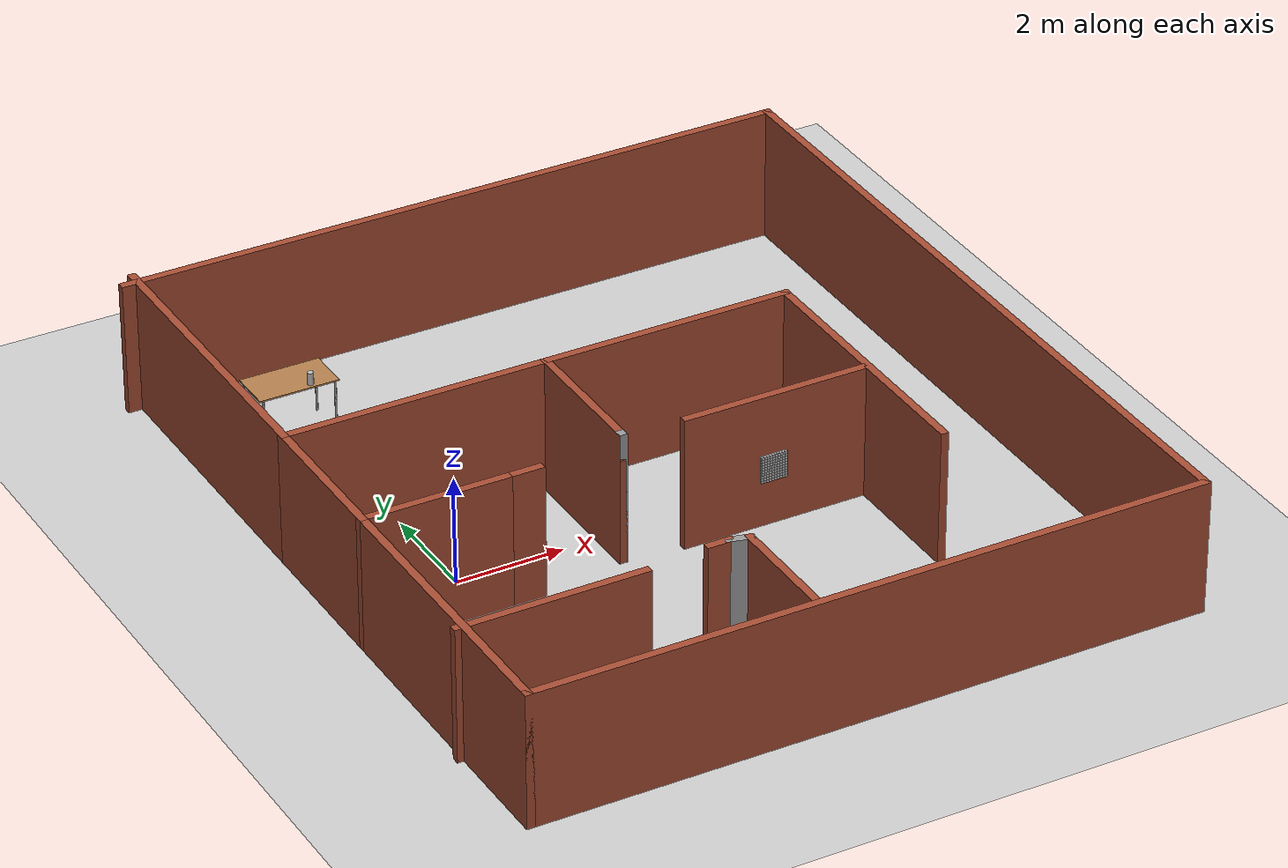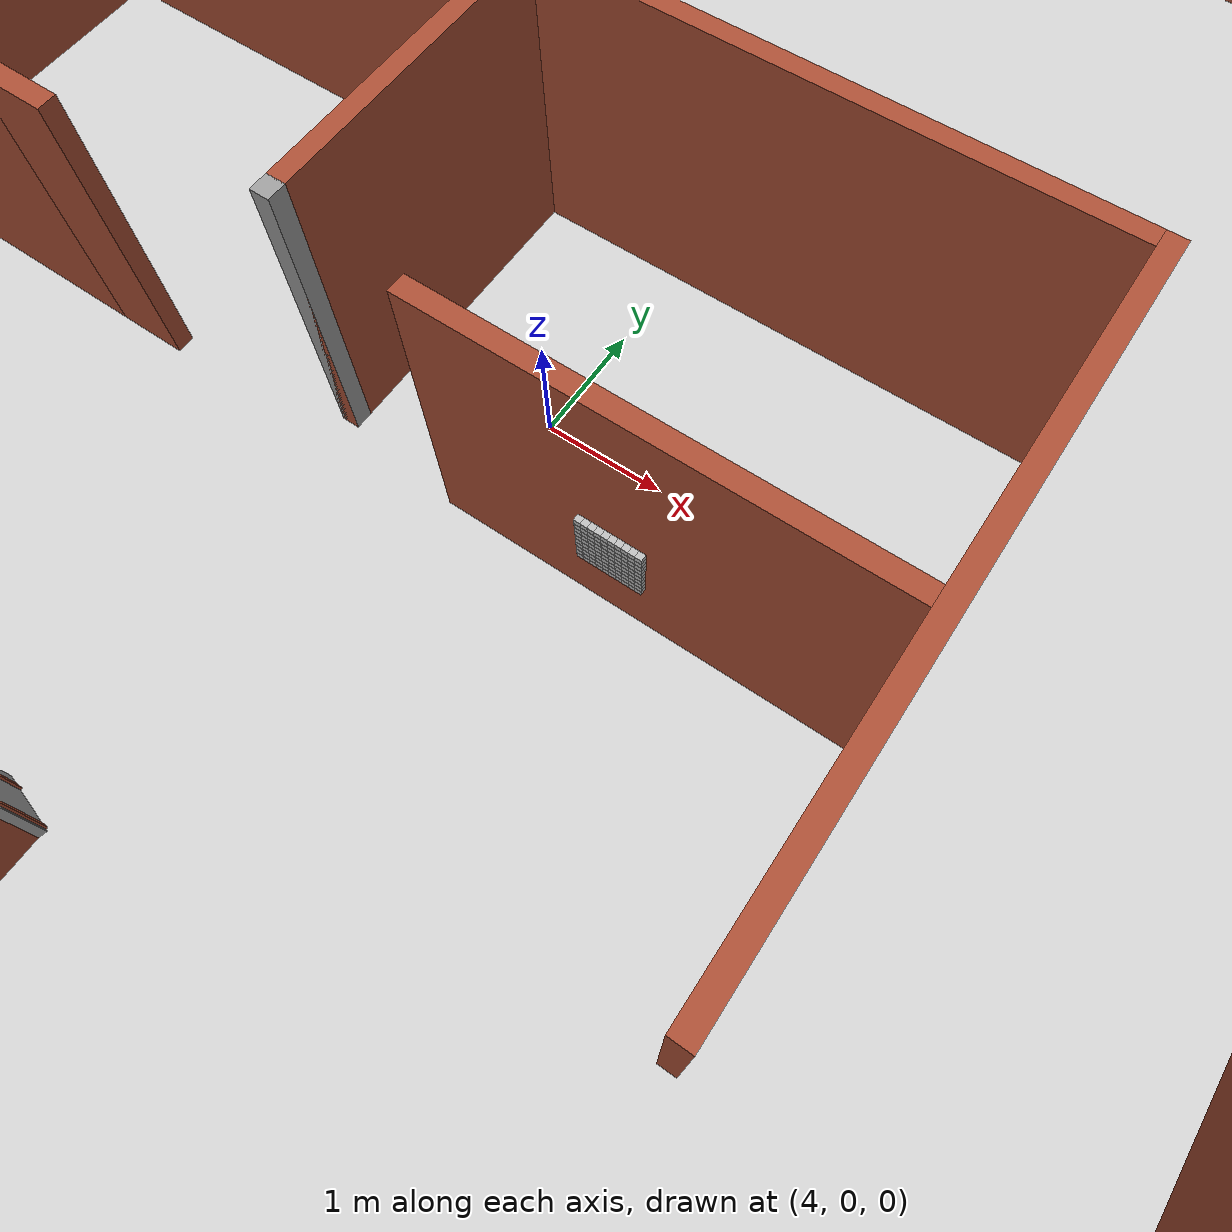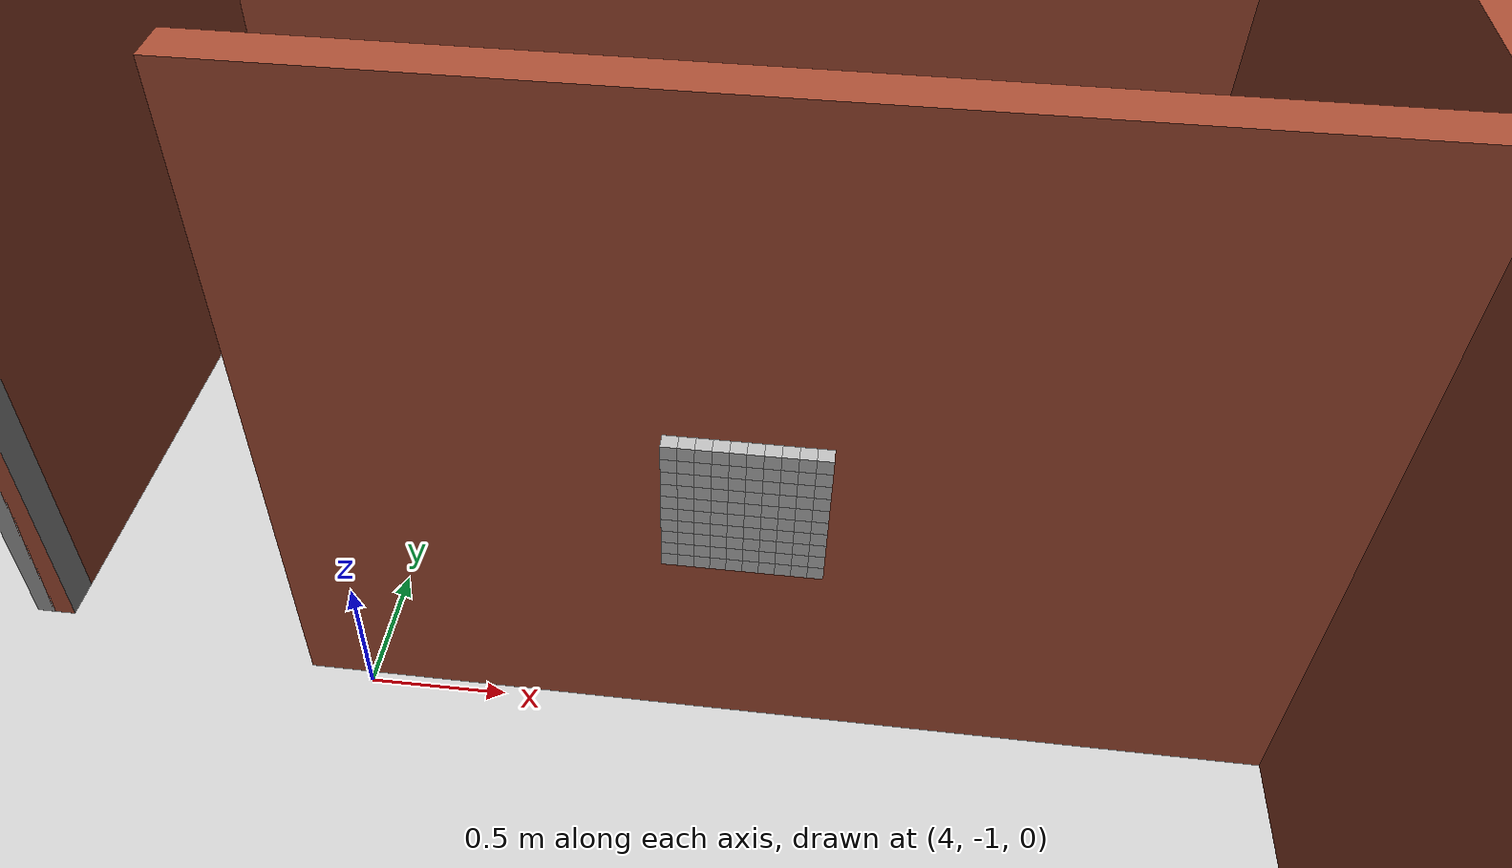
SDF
<sdf version="1.7">
 <world name="default">
  <light name="sun" type="directional">
   <pose>0 0 10 0 -0 0</pose>
   <diffuse>0.8 0.8 0.8 1</diffuse>
   <specular>0.2 0.2 0.2 1</specular>
   <attenuation>
    <range>1000</range>
    <constant>0.9</constant>
    <linear>0.01</linear>
    <quadratic>0.001</quadratic>
   </attenuation>
   <direction>-0.5 0.1 -0.9</direction>
   <spot><inner_angle>0</inner_angle><outer_angle>0</outer_angle><falloff>0</falloff></spot>
  </light>
  <model name="ground_plane">
   <static>1</static>
   <link name="link">
    <collision name="collision">
     <geometry><plane><normal>0 0 1</normal><size>100 100</size></plane></geometry>
     <surface><friction><ode><mu>100</mu><mu2>50</mu2></ode></friction></surface>
    </collision>
    <visual name="visual">
     <cast_shadows>0</cast_shadows>
     <geometry><plane><normal>0 0 1</normal><size>100 100</size></plane></geometry>
     <material>
      <script><uri>file://media/materials/scripts/gazebo.material</uri><name>Gazebo/Grey</name></script>
     </material>
    </visual>
   </link>
  </model>
  <gravity>0 0 -9.8</gravity>
  <magnetic_field>6e-06 2.3e-05 -4.2e-05</magnetic_field>
  <atmosphere type="adiabatic"/>
  <physics type="ode">
   <max_step_size>0.001</max_step_size>
   <real_time_factor>1</real_time_factor>
   <real_time_update_rate>1000</real_time_update_rate>
  </physics>
  <scene><ambient>0.4 0.4 0.4 1</ambient><background>0.7 0.7 0.7 1</background><shadows>1</shadows></scene>
  <spherical_coordinates>
   <surface_model>EARTH_WGS84</surface_model>
   <latitude_deg>0</latitude_deg>
   <longitude_deg>0</longitude_deg>
   <elevation>0</elevation>
   <heading_deg>0</heading_deg>
  </spherical_coordinates>
  <model name="test">
   <pose>3.88587 0.535286 0 0 -0 0</pose>
   <link name="Wall_1">
    <collision name="Wall_1_Collision">
     <geometry><box><size>2.75 0.15 2.5</size></box></geometry>
     <pose>0 0 1.25 0 -0 0</pose>
    </collision>
    <visual name="Wall_1_Visual">
     <pose>0 0 1.25 0 -0 0</pose>
     <geometry><box><size>2.75 0.15 2.5</size></box></geometry>
     <material>
      <script><uri>file://media/materials/scripts/gazebo.material</uri><name>Gazebo/Bricks</name></script>
      <ambient>1 1 1 1</ambient>
     </material>
     <meta><layer>0</layer></meta>
    </visual>
    <pose>-4.75 -1.55 0 0 -0 3.14159</pose>
   </link>
   <link name="Wall_10">
    <collision name="Wall_10_Collision">
     <geometry><box><size>12.5 0.15 2.5</size></box></geometry>
     <pose>0 0 1.25 0 -0 0</pose>
    </collision>
    <visual name="Wall_10_Visual">
     <pose>0 0 1.25 0 -0 0</pose>
     <geometry><box><size>12.5 0.15 2.5</size></box></geometry>
     <material>
      <script><uri>file://media/materials/scripts/gazebo.material</uri><name>Gazebo/Bricks</name></script>
      <ambient>1 1 1 1</ambient>
     </material>
     <meta><layer>0</layer></meta>
    </visual>
    <pose>0.125 -7.15 0 0 -0 0</pose>
   </link>
   <link name="Wall_11">
    <collision name="Wall_11_Collision">
     <geometry><box><size>14.25 0.15 2.5</size></box></geometry>
     <pose>0 0 1.25 0 -0 0</pose>
    </collision>
    <visual name="Wall_11_Visual">
     <pose>0 0 1.25 0 -0 0</pose>
     <geometry><box><size>14.25 0.15 2.5</size></box></geometry>
     <material>
      <script><uri>file://media/materials/scripts/gazebo.material</uri><name>Gazebo/Bricks</name></script>
      <ambient>1 1 1 1</ambient>
     </material>
     <meta><layer>0</layer></meta>
    </visual>
    <pose>6.3 -0.1 0 0 -0 1.5708</pose>
   </link>
   <link name="Wall_12">
    <collision name="Wall_12_Collision">
     <geometry><box><size>12.75 0.15 2.5</size></box></geometry>
     <pose>0 0 1.25 0 -0 0</pose>
    </collision>
    <visual name="Wall_12_Visual">
     <pose>0 0 1.25 0 -0 0</pose>
     <geometry><box><size>12.75 0.15 2.5</size></box></geometry>
     <material>
      <script><uri>file://media/materials/scripts/gazebo.material</uri><name>Gazebo/Bricks</name></script>
      <ambient>1 1 1 1</ambient>
     </material>
     <meta><layer>0</layer></meta>
    </visual>
    <pose>-0 6.95 0 0 -0 3.14159</pose>
   </link>
   <link name="Wall_14">
    <collision name="Wall_14_Collision">
     <geometry><box><size>6 0.15 2.5</size></box></geometry>
     <pose>0 0 1.25 0 -0 0</pose>
    </collision>
    <visual name="Wall_14_Visual">
     <pose>0 0 1.25 0 -0 0</pose>
     <geometry><box><size>6 0.15 2.5</size></box></geometry>
     <material>
      <script><uri>file://media/materials/scripts/gazebo.material</uri><name>Gazebo/Bricks</name></script>
      <ambient>1 1 1 1</ambient>
     </material>
     <meta><layer>0</layer></meta>
    </visual>
    <pose>-6.05 4.225 0 0 -0 1.5708</pose>
   </link>
   <link name="Wall_16">
    <collision name="Wall_16_Collision">
     <geometry><box><size>0.75 0.15 2.5</size></box></geometry>
     <pose>0 0 1.25 0 -0 0</pose>
    </collision>
    <visual name="Wall_16_Visual">
     <pose>0 0 1.25 0 -0 0</pose>
     <geometry><box><size>0.75 0.15 2.5</size></box></geometry>
     <material>
      <script><uri>file://media/materials/scripts/gazebo.material</uri><name>Gazebo/Bricks</name></script>
      <ambient>1 1 1 1</ambient>
     </material>
     <meta><layer>0</layer></meta>
    </visual>
    <pose>-3.15 -1.55 0 0 -0 0</pose>
   </link>
   <link name="Wall_18">
    <collision name="Wall_18_Collision">
     <geometry><box><size>3.5 0.15 2.5</size></box></geometry>
     <pose>0 0 1.25 0 -0 0</pose>
    </collision>
    <visual name="Wall_18_Visual">
     <pose>0 0 1.25 0 -0 0</pose>
     <geometry><box><size>3.5 0.15 2.5</size></box></geometry>
     <material>
      <script><uri>file://media/materials/scripts/gazebo.material</uri><name>Gazebo/Bricks</name></script>
      <ambient>1 1 1 1</ambient>
     </material>
     <meta><layer>0</layer></meta>
    </visual>
    <pose>1.62011 -1.42426 0 0 -0 3.14159</pose>
   </link>
   <link name="Wall_2">
    <collision name="Wall_2_Collision">
     <geometry><box><size>3 0.15 2.5</size></box></geometry>
     <pose>0 0 1.25 0 -0 0</pose>
    </collision>
    <visual name="Wall_2_Visual">
     <pose>0 0 1.25 0 -0 0</pose>
     <geometry><box><size>3 0.15 2.5</size></box></geometry>
     <material>
      <script><uri>file://media/materials/scripts/gazebo.material</uri><name>Gazebo/Bricks</name></script>
      <ambient>1 1 1 1</ambient>
     </material>
     <meta><layer>0</layer></meta>
    </visual>
    <pose>-6.05 -0.125 0 0 -0 1.5708</pose>
   </link>
   <link name="Wall_20">
    <collision name="Wall_20_Collision">
     <geometry><box><size>0.15 0.15 2.5</size></box></geometry>
     <pose>0 0 1.25 0 -0 0</pose>
    </collision>
    <visual name="Wall_20_Visual">
     <pose>0 0 1.25 0 -0 0</pose>
     <geometry><box><size>0.15 0.15 2.5</size></box></geometry>
     <material>
      <script><uri>file://media/materials/scripts/gazebo.material</uri><name>Gazebo/Grey</name></script>
      <ambient>1 1 1 1</ambient>
     </material>
     <meta><layer>0</layer></meta>
    </visual>
    <pose>-1.2 -1.3 0 0 -0 0</pose>
   </link>
   <link name="Wall_22">
    <collision name="Wall_22_Collision">
     <geometry><box><size>3.5 0.15 2.5</size></box></geometry>
     <pose>0 0 1.25 0 -0 0</pose>
    </collision>
    <visual name="Wall_22_Visual">
     <pose>0 0 1.25 0 -0 0</pose>
     <geometry><box><size>3.5 0.15 2.5</size></box></geometry>
     <material>
      <script><uri>file://media/materials/scripts/gazebo.material</uri><name>Gazebo/Bricks</name></script>
      <ambient>1 1 1 1</ambient>
     </material>
     <meta><layer>0</layer></meta>
    </visual>
    <pose>-4.48918 -5.04855 0 0 -0 0</pose>
   </link>
   <link name="Wall_25">
    <collision name="Wall_25_Collision">
     <geometry><box><size>2.25 0.15 2.5</size></box></geometry>
     <pose>0 0 1.25 0 -0 0</pose>
    </collision>
    <visual name="Wall_25_Visual">
     <pose>0 0 1.25 0 -0 0</pose>
     <geometry><box><size>2.25 0.15 2.5</size></box></geometry>
     <material>
      <script><uri>file://media/materials/scripts/gazebo.material</uri><name>Gazebo/Bricks</name></script>
      <ambient>1 1 1 1</ambient>
     </material>
     <meta><layer>0</layer></meta>
    </visual>
    <pose>-0.904959 -6.06179 0 0 -0 1.5708</pose>
   </link>
   <link name="Wall_26">
    <collision name="Wall_26_Collision">
     <geometry><box><size>0.5 0.15 2.5</size></box></geometry>
     <pose>0 0 1.25 0 -0 0</pose>
    </collision>
    <visual name="Wall_26_Visual">
     <pose>0 0 1.25 0 -0 0</pose>
     <geometry><box><size>0.5 0.15 2.5</size></box></geometry>
     <material>
      <script><uri>file://media/materials/scripts/gazebo.material</uri><name>Gazebo/Grey</name></script>
      <ambient>1 1 1 1</ambient>
     </material>
     <meta><layer>0</layer></meta>
    </visual>
    <pose>-1.074 -4.96649 0 0 -0 2.87979</pose>
   </link>
   <link name="Wall_27">
    <collision name="Wall_27_Collision">
     <geometry><box><size>0.5 0.15 2.5</size></box></geometry>
     <pose>0 0 1.25 0 -0 0</pose>
    </collision>
    <visual name="Wall_27_Visual">
     <pose>0 0 1.25 0 -0 0</pose>
     <geometry><box><size>0.5 0.15 2.5</size></box></geometry>
     <material>
      <script><uri>file://media/materials/scripts/gazebo.material</uri><name>Gazebo/Bricks</name></script>
      <ambient>1 1 1 1</ambient>
     </material>
     <meta><layer>0</layer></meta>
    </visual>
    <pose>-1.41803 -4.9212 0 0 -0 3.14159</pose>
   </link>
   <link name="Wall_3">
    <collision name="Wall_3_Collision">
     <geometry><box><size>5 0.15 2.5</size></box></geometry>
     <pose>0 0 1.25 0 -0 0</pose>
    </collision>
    <visual name="Wall_3_Visual">
     <pose>0 0 1.25 0 -0 0</pose>
     <geometry><box><size>5 0.15 2.5</size></box></geometry>
     <material>
      <script><uri>file://media/materials/scripts/gazebo.material</uri><name>Gazebo/Bricks</name></script>
      <ambient>1 1 1 1</ambient>
     </material>
     <meta><layer>0</layer></meta>
    </visual>
    <pose>-3.625 1.3 0 0 -0 0</pose>
   </link>
   <link name="Wall_4">
    <collision name="Wall_4_Collision">
     <geometry><box><size>2.75 0.15 2.5</size></box></geometry>
     <pose>0 0 1.25 0 -0 0</pose>
    </collision>
    <visual name="Wall_4_Visual">
     <pose>0 0 1.25 0 -0 0</pose>
     <geometry><box><size>2.75 0.15 2.5</size></box></geometry>
     <material>
      <script><uri>file://media/materials/scripts/gazebo.material</uri><name>Gazebo/Bricks</name></script>
      <ambient>1 1 1 1</ambient>
     </material>
     <meta><layer>0</layer></meta>
    </visual>
    <pose>-1.2 0 0 0 -0 -1.5708</pose>
   </link>
   <link name="Wall_6">
    <collision name="Wall_6_Collision">
     <geometry><box><size>4.75 0.15 2.5</size></box></geometry>
     <pose>0 0 1.25 0 -0 0</pose>
    </collision>
    <visual name="Wall_6_Visual">
     <pose>0 0 1.25 0 -0 0</pose>
     <geometry><box><size>4.75 0.15 2.5</size></box></geometry>
     <material>
      <script><uri>file://media/materials/scripts/gazebo.material</uri><name>Gazebo/Bricks</name></script>
      <ambient>1 1 1 1</ambient>
     </material>
     <meta><layer>0</layer></meta>
    </visual>
    <pose>1.1 1.3 0 0 -0 0</pose>
   </link>
   <link name="Wall_7">
    <collision name="Wall_7_Collision">
     <geometry><box><size>5.25 0.15 2.5</size></box></geometry>
     <pose>0 0 1.25 0 -0 0</pose>
    </collision>
    <visual name="Wall_7_Visual">
     <pose>0 0 1.25 0 -0 0</pose>
     <geometry><box><size>5.25 0.15 2.5</size></box></geometry>
     <material>
      <script><uri>file://media/materials/scripts/gazebo.material</uri><name>Gazebo/Bricks</name></script>
      <ambient>1 1 1 1</ambient>
     </material>
     <meta><layer>0</layer></meta>
    </visual>
    <pose>3.4 -1.25 0 0 -0 -1.5708</pose>
   </link>
   <link name="Wall_9">
    <collision name="Wall_9_Collision">
     <geometry><box><size>5.75 0.15 2.5</size></box></geometry>
     <pose>0 0 1.25 0 -0 0</pose>
    </collision>
    <visual name="Wall_9_Visual">
     <pose>0 0 1.25 0 -0 0</pose>
     <geometry><box><size>5.75 0.15 2.5</size></box></geometry>
     <material>
      <script><uri>file://media/materials/scripts/gazebo.material</uri><name>Gazebo/Bricks</name></script>
      <ambient>1 1 1 1</ambient>
     </material>
     <meta><layer>0</layer></meta>
    </visual>
    <pose>-6.05 -4.35 0 0 -0 -1.5708</pose>
   </link>
   <static>1</static>
  </model>
  <model name="table">
   <static>1</static>
   <link name="link">
    <collision name="surface">
     <pose>0 0 1 0 -0 0</pose>
     <geometry><box><size>1.5 0.8 0.03</size></box></geometry>
     <surface><friction><ode><mu>0.6</mu><mu2>0.6</mu2></ode></friction></surface>
    </collision>
    <visual name="visual1">
     <pose>0 0 1 0 -0 0</pose>
     <geometry><box><size>1.5 0.8 0.03</size></box></geometry>
     <material>
      <script><uri>file://media/materials/scripts/gazebo.material</uri><name>Gazebo/Wood</name></script>
     </material>
    </visual>
    <collision name="front_left_leg">
     <pose>0.68 0.38 0.5 0 -0 0</pose>
     <geometry><cylinder><radius>0.02</radius><length>1</length></cylinder></geometry>
    </collision>
    <visual name="front_left_leg">
     <pose>0.68 0.38 0.5 0 -0 0</pose>
     <geometry><cylinder><radius>0.02</radius><length>1</length></cylinder></geometry>
     <material>
      <script><uri>file://media/materials/scripts/gazebo.material</uri><name>Gazebo/Grey</name></script>
     </material>
    </visual>
    <collision name="front_right_leg">
     <pose>0.68 -0.38 0.5 0 -0 0</pose>
     <geometry><cylinder><radius>0.02</radius><length>1</length></cylinder></geometry>
    </collision>
    <visual name="front_right_leg">
     <pose>0.68 -0.38 0.5 0 -0 0</pose>
     <geometry><cylinder><radius>0.02</radius><length>1</length></cylinder></geometry>
     <material>
      <script><uri>file://media/materials/scripts/gazebo.material</uri><name>Gazebo/Grey</name></script>
     </material>
    </visual>
    <collision name="back_right_leg">
     <pose>-0.68 -0.38 0.5 0 -0 0</pose>
     <geometry><cylinder><radius>0.02</radius><length>1</length></cylinder></geometry>
    </collision>
    <visual name="back_right_leg">
     <pose>-0.68 -0.38 0.5 0 -0 0</pose>
     <geometry><cylinder><radius>0.02</radius><length>1</length></cylinder></geometry>
     <material>
      <script><uri>file://media/materials/scripts/gazebo.material</uri><name>Gazebo/Grey</name></script>
     </material>
    </visual>
    <collision name="back_left_leg">
     <pose>-0.68 0.38 0.5 0 -0 0</pose>
     <geometry><cylinder><radius>0.02</radius><length>1</length></cylinder></geometry>
    </collision>
    <visual name="back_left_leg">
     <pose>-0.68 0.38 0.5 0 -0 0</pose>
     <geometry><cylinder><radius>0.02</radius><length>1</length></cylinder></geometry>
     <material>
      <script><uri>file://media/materials/scripts/gazebo.material</uri><name>Gazebo/Grey</name></script>
     </material>
    </visual>
   </link>
   <pose>-0.296239 5.55445 0 0 -0 0</pose>
  </model>
  <model name="breakable_test">
   <pose>5.1395 -1.12375 0.996693 0 -0 0</pose>
   <link name="link_0_0">
    <inertial>
     <mass>0.3375</mass>
     <inertia>
      <ixx>0.000140625</ixx>
      <iyy>0.000140625</iyy>
      <izz>0.000140625</izz>
      <ixy>0</ixy>
      <ixz>0</ixz>
      <iyz>0</iyz>
     </inertia>
    </inertial>
    <collision name="collision"><geometry><box><size>0.05 0.05 0.05</size></box></geometry></collision>
    <visual name="visual"><geometry><box><size>0.05 0.05 0.05</size></box></geometry></visual>
   </link>
   <joint name="joint_0_0" type="revolute">
    <parent>world</parent>
    <child>link_0_0</child>
    <axis>
     <xyz expressed_in="__model__">0 0 1</xyz>
     <limit><lower>0</lower><upper>0</upper></limit>
     <dynamics><spring_reference>0</spring_reference><spring_stiffness>0</spring_stiffness></dynamics>
    </axis>
    <physics><ode><erp>1</erp><cfm>1</cfm><limit><cfm>0</cfm><erp>0.2</erp></limit></ode></physics>
    <sensor name="force_torque" type="force_torque">
     <always_on>1</always_on>
     <update_rate>1000</update_rate>
     <plugin name="breakable_0_0" filename="libBreakableJointPlugin.so">
      <breaking_force_N>50</breaking_force_N>
     </plugin>
    </sensor>
   </joint>
   <link name="link_0_1">
    <pose>0 0 0.05 0 -0 0</pose>
    <inertial>
     <mass>0.3375</mass>
     <inertia>
      <ixx>0.000140625</ixx>
      <iyy>0.000140625</iyy>
      <izz>0.000140625</izz>
      <ixy>0</ixy>
      <ixz>0</ixz>
      <iyz>0</iyz>
     </inertia>
    </inertial>
    <collision name="collision"><geometry><box><size>0.05 0.05 0.05</size></box></geometry></collision>
    <visual name="visual"><geometry><box><size>0.05 0.05 0.05</size></box></geometry></visual>
   </link>
   <joint name="joint_0_1" type="revolute">
    <parent>world</parent>
    <child>link_0_1</child>
    <axis>
     <xyz expressed_in="__model__">0 0 1</xyz>
     <limit><lower>0</lower><upper>0</upper></limit>
     <dynamics><spring_reference>0</spring_reference><spring_stiffness>0</spring_stiffness></dynamics>
    </axis>
    <physics><ode><erp>1</erp><cfm>1</cfm><limit><cfm>0</cfm><erp>0.2</erp></limit></ode></physics>
    <sensor name="force_torque" type="force_torque">
     <always_on>1</always_on>
     <update_rate>1000</update_rate>
     <plugin name="breakable_0_1" filename="libBreakableJointPlugin.so">
      <breaking_force_N>50</breaking_force_N>
     </plugin>
    </sensor>
   </joint>
   <link name="link_0_2">
    <pose>0 0 0.1 0 -0 0</pose>
    <inertial>
     <mass>0.3375</mass>
     <inertia>
      <ixx>0.000140625</ixx>
      <iyy>0.000140625</iyy>
      <izz>0.000140625</izz>
      <ixy>0</ixy>
      <ixz>0</ixz>
      <iyz>0</iyz>
     </inertia>
    </inertial>
    <collision name="collision"><geometry><box><size>0.05 0.05 0.05</size></box></geometry></collision>
    <visual name="visual"><geometry><box><size>0.05 0.05 0.05</size></box></geometry></visual>
   </link>
   <joint name="joint_0_2" type="revolute">
    <parent>world</parent>
    <child>link_0_2</child>
    <axis>
     <xyz expressed_in="__model__">0 0 1</xyz>
     <limit><lower>0</lower><upper>0</upper></limit>
     <dynamics><spring_reference>0</spring_reference><spring_stiffness>0</spring_stiffness></dynamics>
    </axis>
    <physics><ode><erp>1</erp><cfm>1</cfm><limit><cfm>0</cfm><erp>0.2</erp></limit></ode></physics>
    <sensor name="force_torque" type="force_torque">
     <always_on>1</always_on>
     <update_rate>1000</update_rate>
     <plugin name="breakable_0_2" filename="libBreakableJointPlugin.so">
      <breaking_force_N>50</breaking_force_N>
     </plugin>
    </sensor>
   </joint>
   <link name="link_0_3">
    <pose>0 0 0.15 0 -0 0</pose>
    <inertial>
     <mass>0.3375</mass>
     <inertia>
      <ixx>0.000140625</ixx>
      <iyy>0.000140625</iyy>
      <izz>0.000140625</izz>
      <ixy>0</ixy>
      <ixz>0</ixz>
      <iyz>0</iyz>
     </inertia>
    </inertial>
    <collision name="collision"><geometry><box><size>0.05 0.05 0.05</size></box></geometry></collision>
    <visual name="visual"><geometry><box><size>0.05 0.05 0.05</size></box></geometry></visual>
   </link>
   <joint name="joint_0_3" type="revolute">
    <parent>world</parent>
    <child>link_0_3</child>
    <axis>
     <xyz expressed_in="__model__">0 0 1</xyz>
     <limit><lower>0</lower><upper>0</upper></limit>
     <dynamics><spring_reference>0</spring_reference><spring_stiffness>0</spring_stiffness></dynamics>
    </axis>
    <physics><ode><erp>1</erp><cfm>1</cfm><limit><cfm>0</cfm><erp>0.2</erp></limit></ode></physics>
    <sensor name="force_torque" type="force_torque">
     <always_on>1</always_on>
     <update_rate>1000</update_rate>
     <plugin name="breakable_0_3" filename="libBreakableJointPlugin.so">
      <breaking_force_N>50</breaking_force_N>
     </plugin>
    </sensor>
   </joint>
   <link name="link_0_4">
    <pose>0 0 0.2 0 -0 0</pose>
    <inertial>
     <mass>0.3375</mass>
     <inertia>
      <ixx>0.000140625</ixx>
      <iyy>0.000140625</iyy>
      <izz>0.000140625</izz>
      <ixy>0</ixy>
      <ixz>0</ixz>
      <iyz>0</iyz>
     </inertia>
    </inertial>
    <collision name="collision"><geometry><box><size>0.05 0.05 0.05</size></box></geometry></collision>
    <visual name="visual"><geometry><box><size>0.05 0.05 0.05</size></box></geometry></visual>
   </link>
   <joint name="joint_0_4" type="revolute">
    <parent>world</parent>
    <child>link_0_4</child>
    <axis>
     <xyz expressed_in="__model__">0 0 1</xyz>
     <limit><lower>0</lower><upper>0</upper></limit>
     <dynamics><spring_reference>0</spring_reference><spring_stiffness>0</spring_stiffness></dynamics>
    </axis>
    <physics><ode><erp>1</erp><cfm>1</cfm><limit><cfm>0</cfm><erp>0.2</erp></limit></ode></physics>
    <sensor name="force_torque" type="force_torque">
     <always_on>1</always_on>
     <update_rate>1000</update_rate>
     <plugin name="breakable_0_4" filename="libBreakableJointPlugin.so">
      <breaking_force_N>50</breaking_force_N>
     </plugin>
    </sensor>
   </joint>
   <link name="link_0_5">
    <pose>0 0 0.25 0 -0 0</pose>
    <inertial>
     <mass>0.3375</mass>
     <inertia>
      <ixx>0.000140625</ixx>
      <iyy>0.000140625</iyy>
      <izz>0.000140625</izz>
      <ixy>0</ixy>
      <ixz>0</ixz>
      <iyz>0</iyz>
     </inertia>
    </inertial>
    <collision name="collision"><geometry><box><size>0.05 0.05 0.05</size></box></geometry></collision>
    <visual name="visual"><geometry><box><size>0.05 0.05 0.05</size></box></geometry></visual>
   </link>
   <joint name="joint_0_5" type="revolute">
    <parent>world</parent>
    <child>link_0_5</child>
    <axis>
     <xyz expressed_in="__model__">0 0 1</xyz>
     <limit><lower>0</lower><upper>0</upper></limit>
     <dynamics><spring_reference>0</spring_reference><spring_stiffness>0</spring_stiffness></dynamics>
    </axis>
    <physics><ode><erp>1</erp><cfm>1</cfm><limit><cfm>0</cfm><erp>0.2</erp></limit></ode></physics>
    <sensor name="force_torque" type="force_torque">
     <always_on>1</always_on>
     <update_rate>1000</update_rate>
     <plugin name="breakable_0_5" filename="libBreakableJointPlugin.so">
      <breaking_force_N>50</breaking_force_N>
     </plugin>
    </sensor>
   </joint>
   <link name="link_0_6">
    <pose>0 0 0.3 0 -0 0</pose>
    <inertial>
     <mass>0.3375</mass>
     <inertia>
      <ixx>0.000140625</ixx>
      <iyy>0.000140625</iyy>
      <izz>0.000140625</izz>
      <ixy>0</ixy>
      <ixz>0</ixz>
      <iyz>0</iyz>
     </inertia>
    </inertial>
    <collision name="collision"><geometry><box><size>0.05 0.05 0.05</size></box></geometry></collision>
    <visual name="visual"><geometry><box><size>0.05 0.05 0.05</size></box></geometry></visual>
   </link>
   <joint name="joint_0_6" type="revolute">
    <parent>world</parent>
    <child>link_0_6</child>
    <axis>
     <xyz expressed_in="__model__">0 0 1</xyz>
     <limit><lower>0</lower><upper>0</upper></limit>
     <dynamics><spring_reference>0</spring_reference><spring_stiffness>0</spring_stiffness></dynamics>
    </axis>
    <physics><ode><erp>1</erp><cfm>1</cfm><limit><cfm>0</cfm><erp>0.2</erp></limit></ode></physics>
    <sensor name="force_torque" type="force_torque">
     <always_on>1</always_on>
     <update_rate>1000</update_rate>
     <plugin name="breakable_0_6" filename="libBreakableJointPlugin.so">
      <breaking_force_N>50</breaking_force_N>
     </plugin>
    </sensor>
   </joint>
   <link name="link_0_7">
    <pose>0 0 0.35 0 -0 0</pose>
    <inertial>
     <mass>0.3375</mass>
     <inertia>
      <ixx>0.000140625</ixx>
      <iyy>0.000140625</iyy>
      <izz>0.000140625</izz>
      <ixy>0</ixy>
      <ixz>0</ixz>
      <iyz>0</iyz>
     </inertia>
    </inertial>
    <collision name="collision"><geometry><box><size>0.05 0.05 0.05</size></box></geometry></collision>
    <visual name="visual"><geometry><box><size>0.05 0.05 0.05</size></box></geometry></visual>
   </link>
   <joint name="joint_0_7" type="revolute">
    <parent>world</parent>
    <child>link_0_7</child>
    <axis>
     <xyz expressed_in="__model__">0 0 1</xyz>
     <limit><lower>0</lower><upper>0</upper></limit>
     <dynamics><spring_reference>0</spring_reference><spring_stiffness>0</spring_stiffness></dynamics>
    </axis>
    <physics><ode><erp>1</erp><cfm>1</cfm><limit><cfm>0</cfm><erp>0.2</erp></limit></ode></physics>
    <sensor name="force_torque" type="force_torque">
     <always_on>1</always_on>
     <update_rate>1000</update_rate>
     <plugin name="breakable_0_7" filename="libBreakableJointPlugin.so">
      <breaking_force_N>50</breaking_force_N>
     </plugin>
    </sensor>
   </joint>
   <link name="link_0_8">
    <pose>0 0 0.4 0 -0 0</pose>
    <inertial>
     <mass>0.3375</mass>
     <inertia>
      <ixx>0.000140625</ixx>
      <iyy>0.000140625</iyy>
      <izz>0.000140625</izz>
      <ixy>0</ixy>
      <ixz>0</ixz>
      <iyz>0</iyz>
     </inertia>
    </inertial>
    <collision name="collision"><geometry><box><size>0.05 0.05 0.05</size></box></geometry></collision>
    <visual name="visual"><geometry><box><size>0.05 0.05 0.05</size></box></geometry></visual>
   </link>
   <joint name="joint_0_8" type="revolute">
    <parent>world</parent>
    <child>link_0_8</child>
    <axis>
     <xyz expressed_in="__model__">0 0 1</xyz>
     <limit><lower>0</lower><upper>0</upper></limit>
     <dynamics><spring_reference>0</spring_reference><spring_stiffness>0</spring_stiffness></dynamics>
    </axis>
    <physics><ode><erp>1</erp><cfm>1</cfm><limit><cfm>0</cfm><erp>0.2</erp></limit></ode></physics>
    <sensor name="force_torque" type="force_torque">
     <always_on>1</always_on>
     <update_rate>1000</update_rate>
     <plugin name="breakable_0_8" filename="libBreakableJointPlugin.so">
      <breaking_force_N>50</breaking_force_N>
     </plugin>
    </sensor>
   </joint>
   <link name="link_0_9">
    <pose>0 0 0.45 0 -0 0</pose>
    <inertial>
     <mass>0.3375</mass>
     <inertia>
      <ixx>0.000140625</ixx>
      <iyy>0.000140625</iyy>
      <izz>0.000140625</izz>
      <ixy>0</ixy>
      <ixz>0</ixz>
      <iyz>0</iyz>
     </inertia>
    </inertial>
    <collision name="collision"><geometry><box><size>0.05 0.05 0.05</size></box></geometry></collision>
    <visual name="visual"><geometry><box><size>0.05 0.05 0.05</size></box></geometry></visual>
   </link>
   <joint name="joint_0_9" type="revolute">
    <parent>world</parent>
    <child>link_0_9</child>
    <axis>
     <xyz expressed_in="__model__">0 0 1</xyz>
     <limit><lower>0</lower><upper>0</upper></limit>
     <dynamics><spring_reference>0</spring_reference><spring_stiffness>0</spring_stiffness></dynamics>
    </axis>
    <physics><ode><erp>1</erp><cfm>1</cfm><limit><cfm>0</cfm><erp>0.2</erp></limit></ode></physics>
    <sensor name="force_torque" type="force_torque">
     <always_on>1</always_on>
     <update_rate>1000</update_rate>
     <plugin name="breakable_0_9" filename="libBreakableJointPlugin.so">
      <breaking_force_N>50</breaking_force_N>
     </plugin>
    </sensor>
   </joint>
   <link name="link_1_0">
    <pose>0.05 0 0 0 -0 0</pose>
    <inertial>
     <mass>0.3375</mass>
     <inertia>
      <ixx>0.000140625</ixx>
      <iyy>0.000140625</iyy>
      <izz>0.000140625</izz>
      <ixy>0</ixy>
      <ixz>0</ixz>
      <iyz>0</iyz>
     </inertia>
    </inertial>
    <collision name="collision"><geometry><box><size>0.05 0.05 0.05</size></box></geometry></collision>
    <visual name="visual"><geometry><box><size>0.05 0.05 0.05</size></box></geometry></visual>
   </link>
   <joint name="joint_1_0" type="revolute">
    <parent>world</parent>
    <child>link_1_0</child>
    <axis>
     <xyz expressed_in="__model__">0 0 1</xyz>
     <limit><lower>0</lower><upper>0</upper></limit>
     <dynamics><spring_reference>0</spring_reference><spring_stiffness>0</spring_stiffness></dynamics>
    </axis>
    <physics><ode><erp>1</erp><cfm>1</cfm><limit><cfm>0</cfm><erp>0.2</erp></limit></ode></physics>
    <sensor name="force_torque" type="force_torque">
     <always_on>1</always_on>
     <update_rate>1000</update_rate>
     <plugin name="breakable_1_0" filename="libBreakableJointPlugin.so">
      <breaking_force_N>50</breaking_force_N>
     </plugin>
    </sensor>
   </joint>
   <link name="link_1_1">
    <pose>0.05 0 0.05 0 -0 0</pose>
    <inertial>
     <mass>0.3375</mass>
     <inertia>
      <ixx>0.000140625</ixx>
      <iyy>0.000140625</iyy>
      <izz>0.000140625</izz>
      <ixy>0</ixy>
      <ixz>0</ixz>
      <iyz>0</iyz>
     </inertia>
    </inertial>
    <collision name="collision"><geometry><box><size>0.05 0.05 0.05</size></box></geometry></collision>
    <visual name="visual"><geometry><box><size>0.05 0.05 0.05</size></box></geometry></visual>
   </link>
   <joint name="joint_1_1" type="revolute">
    <parent>world</parent>
    <child>link_1_1</child>
    <axis>
     <xyz expressed_in="__model__">0 0 1</xyz>
     <limit><lower>0</lower><upper>0</upper></limit>
     <dynamics><spring_reference>0</spring_reference><spring_stiffness>0</spring_stiffness></dynamics>
    </axis>
    <physics><ode><erp>1</erp><cfm>1</cfm><limit><cfm>0</cfm><erp>0.2</erp></limit></ode></physics>
    <sensor name="force_torque" type="force_torque">
     <always_on>1</always_on>
     <update_rate>1000</update_rate>
     <plugin name="breakable_1_1" filename="libBreakableJointPlugin.so">
      <breaking_force_N>50</breaking_force_N>
     </plugin>
    </sensor>
   </joint>
   <link name="link_1_2">
    <pose>0.05 0 0.1 0 -0 0</pose>
    <inertial>
     <mass>0.3375</mass>
     <inertia>
      <ixx>0.000140625</ixx>
      <iyy>0.000140625</iyy>
      <izz>0.000140625</izz>
      <ixy>0</ixy>
      <ixz>0</ixz>
      <iyz>0</iyz>
     </inertia>
    </inertial>
    <collision name="collision"><geometry><box><size>0.05 0.05 0.05</size></box></geometry></collision>
    <visual name="visual"><geometry><box><size>0.05 0.05 0.05</size></box></geometry></visual>
   </link>
   <joint name="joint_1_2" type="revolute">
    <parent>world</parent>
    <child>link_1_2</child>
    <axis>
     <xyz expressed_in="__model__">0 0 1</xyz>
     <limit><lower>0</lower><upper>0</upper></limit>
     <dynamics><spring_reference>0</spring_reference><spring_stiffness>0</spring_stiffness></dynamics>
    </axis>
    <physics><ode><erp>1</erp><cfm>1</cfm><limit><cfm>0</cfm><erp>0.2</erp></limit></ode></physics>
    <sensor name="force_torque" type="force_torque">
     <always_on>1</always_on>
     <update_rate>1000</update_rate>
     <plugin name="breakable_1_2" filename="libBreakableJointPlugin.so">
      <breaking_force_N>50</breaking_force_N>
     </plugin>
    </sensor>
   </joint>
   <link name="link_1_3">
    <pose>0.05 0 0.15 0 -0 0</pose>
    <inertial>
     <mass>0.3375</mass>
     <inertia>
      <ixx>0.000140625</ixx>
      <iyy>0.000140625</iyy>
      <izz>0.000140625</izz>
      <ixy>0</ixy>
      <ixz>0</ixz>
      <iyz>0</iyz>
     </inertia>
    </inertial>
    <collision name="collision"><geometry><box><size>0.05 0.05 0.05</size></box></geometry></collision>
    <visual name="visual"><geometry><box><size>0.05 0.05 0.05</size></box></geometry></visual>
   </link>
   <joint name="joint_1_3" type="revolute">
    <parent>world</parent>
    <child>link_1_3</child>
    <axis>
     <xyz expressed_in="__model__">0 0 1</xyz>
     <limit><lower>0</lower><upper>0</upper></limit>
     <dynamics><spring_reference>0</spring_reference><spring_stiffness>0</spring_stiffness></dynamics>
    </axis>
    <physics><ode><erp>1</erp><cfm>1</cfm><limit><cfm>0</cfm><erp>0.2</erp></limit></ode></physics>
    <sensor name="force_torque" type="force_torque">
     <always_on>1</always_on>
     <update_rate>1000</update_rate>
     <plugin name="breakable_1_3" filename="libBreakableJointPlugin.so">
      <breaking_force_N>50</breaking_force_N>
     </plugin>
    </sensor>
   </joint>
   <link name="link_1_4">
    <pose>0.05 0 0.2 0 -0 0</pose>
    <inertial>
     <mass>0.3375</mass>
     <inertia>
      <ixx>0.000140625</ixx>
      <iyy>0.000140625</iyy>
      <izz>0.000140625</izz>
      <ixy>0</ixy>
      <ixz>0</ixz>
      <iyz>0</iyz>
     </inertia>
    </inertial>
    <collision name="collision"><geometry><box><size>0.05 0.05 0.05</size></box></geometry></collision>
    <visual name="visual"><geometry><box><size>0.05 0.05 0.05</size></box></geometry></visual>
   </link>
   <joint name="joint_1_4" type="revolute">
    <parent>world</parent>
    <child>link_1_4</child>
    <axis>
     <xyz expressed_in="__model__">0 0 1</xyz>
     <limit><lower>0</lower><upper>0</upper></limit>
     <dynamics><spring_reference>0</spring_reference><spring_stiffness>0</spring_stiffness></dynamics>
    </axis>
    <physics><ode><erp>1</erp><cfm>1</cfm><limit><cfm>0</cfm><erp>0.2</erp></limit></ode></physics>
    <sensor name="force_torque" type="force_torque">
     <always_on>1</always_on>
     <update_rate>1000</update_rate>
     <plugin name="breakable_1_4" filename="libBreakableJointPlugin.so">
      <breaking_force_N>50</breaking_force_N>
     </plugin>
    </sensor>
   </joint>
   <link name="link_1_5">
    <pose>0.05 0 0.25 0 -0 0</pose>
    <inertial>
     <mass>0.3375</mass>
     <inertia>
      <ixx>0.000140625</ixx>
      <iyy>0.000140625</iyy>
      <izz>0.000140625</izz>
      <ixy>0</ixy>
      <ixz>0</ixz>
      <iyz>0</iyz>
     </inertia>
    </inertial>
    <collision name="collision"><geometry><box><size>0.05 0.05 0.05</size></box></geometry></collision>
    <visual name="visual"><geometry><box><size>0.05 0.05 0.05</size></box></geometry></visual>
   </link>
   <joint name="joint_1_5" type="revolute">
    <parent>world</parent>
    <child>link_1_5</child>
    <axis>
     <xyz expressed_in="__model__">0 0 1</xyz>
     <limit><lower>0</lower><upper>0</upper></limit>
     <dynamics><spring_reference>0</spring_reference><spring_stiffness>0</spring_stiffness></dynamics>
    </axis>
    <physics><ode><erp>1</erp><cfm>1</cfm><limit><cfm>0</cfm><erp>0.2</erp></limit></ode></physics>
    <sensor name="force_torque" type="force_torque">
     <always_on>1</always_on>
     <update_rate>1000</update_rate>
     <plugin name="breakable_1_5" filename="libBreakableJointPlugin.so">
      <breaking_force_N>50</breaking_force_N>
     </plugin>
    </sensor>
   </joint>
   <link name="link_1_6">
    <pose>0.05 0 0.3 0 -0 0</pose>
    <inertial>
     <mass>0.3375</mass>
     <inertia>
      <ixx>0.000140625</ixx>
      <iyy>0.000140625</iyy>
      <izz>0.000140625</izz>
      <ixy>0</ixy>
      <ixz>0</ixz>
      <iyz>0</iyz>
     </inertia>
    </inertial>
    <collision name="collision"><geometry><box><size>0.05 0.05 0.05</size></box></geometry></collision>
    <visual name="visual"><geometry><box><size>0.05 0.05 0.05</size></box></geometry></visual>
   </link>
   <joint name="joint_1_6" type="revolute">
    <parent>world</parent>
    <child>link_1_6</child>
    <axis>
     <xyz expressed_in="__model__">0 0 1</xyz>
     <limit><lower>0</lower><upper>0</upper></limit>
     <dynamics><spring_reference>0</spring_reference><spring_stiffness>0</spring_stiffness></dynamics>
    </axis>
    <physics><ode><erp>1</erp><cfm>1</cfm><limit><cfm>0</cfm><erp>0.2</erp></limit></ode></physics>
    <sensor name="force_torque" type="force_torque">
     <always_on>1</always_on>
     <update_rate>1000</update_rate>
     <plugin name="breakable_1_6" filename="libBreakableJointPlugin.so">
      <breaking_force_N>50</breaking_force_N>
     </plugin>
    </sensor>
   </joint>
   <link name="link_1_7">
    <pose>0.05 0 0.35 0 -0 0</pose>
    <inertial>
     <mass>0.3375</mass>
     <inertia>
      <ixx>0.000140625</ixx>
      <iyy>0.000140625</iyy>
      <izz>0.000140625</izz>
      <ixy>0</ixy>
      <ixz>0</ixz>
      <iyz>0</iyz>
     </inertia>
    </inertial>
    <collision name="collision"><geometry><box><size>0.05 0.05 0.05</size></box></geometry></collision>
    <visual name="visual"><geometry><box><size>0.05 0.05 0.05</size></box></geometry></visual>
   </link>
   <joint name="joint_1_7" type="revolute">
    <parent>world</parent>
    <child>link_1_7</child>
    <axis>
     <xyz expressed_in="__model__">0 0 1</xyz>
     <limit><lower>0</lower><upper>0</upper></limit>
     <dynamics><spring_reference>0</spring_reference><spring_stiffness>0</spring_stiffness></dynamics>
    </axis>
    <physics><ode><erp>1</erp><cfm>1</cfm><limit><cfm>0</cfm><erp>0.2</erp></limit></ode></physics>
    <sensor name="force_torque" type="force_torque">
     <always_on>1</always_on>
     <update_rate>1000</update_rate>
     <plugin name="breakable_1_7" filename="libBreakableJointPlugin.so">
      <breaking_force_N>50</breaking_force_N>
     </plugin>
    </sensor>
   </joint>
   <link name="link_1_8">
    <pose>0.05 0 0.4 0 -0 0</pose>
    <inertial>
     <mass>0.3375</mass>
     <inertia>
      <ixx>0.000140625</ixx>
      <iyy>0.000140625</iyy>
      <izz>0.000140625</izz>
      <ixy>0</ixy>
      <ixz>0</ixz>
      <iyz>0</iyz>
     </inertia>
    </inertial>
    <collision name="collision"><geometry><box><size>0.05 0.05 0.05</size></box></geometry></collision>
    <visual name="visual"><geometry><box><size>0.05 0.05 0.05</size></box></geometry></visual>
   </link>
   <joint name="joint_1_8" type="revolute">
    <parent>world</parent>
    <child>link_1_8</child>
    <axis>
     <xyz expressed_in="__model__">0 0 1</xyz>
     <limit><lower>0</lower><upper>0</upper></limit>
     <dynamics><spring_reference>0</spring_reference><spring_stiffness>0</spring_stiffness></dynamics>
    </axis>
    <physics><ode><erp>1</erp><cfm>1</cfm><limit><cfm>0</cfm><erp>0.2</erp></limit></ode></physics>
    <sensor name="force_torque" type="force_torque">
     <always_on>1</always_on>
     <update_rate>1000</update_rate>
     <plugin name="breakable_1_8" filename="libBreakableJointPlugin.so">
      <breaking_force_N>50</breaking_force_N>
     </plugin>
    </sensor>
   </joint>
   <link name="link_1_9">
    <pose>0.05 0 0.45 0 -0 0</pose>
    <inertial>
     <mass>0.3375</mass>
     <inertia>
      <ixx>0.000140625</ixx>
      <iyy>0.000140625</iyy>
      <izz>0.000140625</izz>
      <ixy>0</ixy>
      <ixz>0</ixz>
      <iyz>0</iyz>
     </inertia>
    </inertial>
    <collision name="collision"><geometry><box><size>0.05 0.05 0.05</size></box></geometry></collision>
    <visual name="visual"><geometry><box><size>0.05 0.05 0.05</size></box></geometry></visual>
   </link>
   <joint name="joint_1_9" type="revolute">
    <parent>world</parent>
    <child>link_1_9</child>
    <axis>
     <xyz expressed_in="__model__">0 0 1</xyz>
     <limit><lower>0</lower><upper>0</upper></limit>
     <dynamics><spring_reference>0</spring_reference><spring_stiffness>0</spring_stiffness></dynamics>
    </axis>
    <physics><ode><erp>1</erp><cfm>1</cfm><limit><cfm>0</cfm><erp>0.2</erp></limit></ode></physics>
    <sensor name="force_torque" type="force_torque">
     <always_on>1</always_on>
     <update_rate>1000</update_rate>
     <plugin name="breakable_1_9" filename="libBreakableJointPlugin.so">
      <breaking_force_N>50</breaking_force_N>
     </plugin>
    </sensor>
   </joint>
   <link name="link_2_0">
    <pose>0.1 0 0 0 -0 0</pose>
    <inertial>
     <mass>0.3375</mass>
     <inertia>
      <ixx>0.000140625</ixx>
      <iyy>0.000140625</iyy>
      <izz>0.000140625</izz>
      <ixy>0</ixy>
      <ixz>0</ixz>
      <iyz>0</iyz>
     </inertia>
    </inertial>
    <collision name="collision"><geometry><box><size>0.05 0.05 0.05</size></box></geometry></collision>
    <visual name="visual"><geometry><box><size>0.05 0.05 0.05</size></box></geometry></visual>
   </link>
   <joint name="joint_2_0" type="revolute">
    <parent>world</parent>
    <child>link_2_0</child>
    <axis>
     <xyz expressed_in="__model__">0 0 1</xyz>
     <limit><lower>0</lower><upper>0</upper></limit>
     <dynamics><spring_reference>0</spring_reference><spring_stiffness>0</spring_stiffness></dynamics>
    </axis>
    <physics><ode><erp>1</erp><cfm>1</cfm><limit><cfm>0</cfm><erp>0.2</erp></limit></ode></physics>
    <sensor name="force_torque" type="force_torque">
     <always_on>1</always_on>
     <update_rate>1000</update_rate>
     <plugin name="breakable_2_0" filename="libBreakableJointPlugin.so">
      <breaking_force_N>50</breaking_force_N>
     </plugin>
    </sensor>
   </joint>
   <link name="link_2_1">
    <pose>0.1 0 0.05 0 -0 0</pose>
    <inertial>
     <mass>0.3375</mass>
     <inertia>
      <ixx>0.000140625</ixx>
      <iyy>0.000140625</iyy>
      <izz>0.000140625</izz>
      <ixy>0</ixy>
      <ixz>0</ixz>
      <iyz>0</iyz>
     </inertia>
    </inertial>
    <collision name="collision"><geometry><box><size>0.05 0.05 0.05</size></box></geometry></collision>
    <visual name="visual"><geometry><box><size>0.05 0.05 0.05</size></box></geometry></visual>
   </link>
   <joint name="joint_2_1" type="revolute">
    <parent>world</parent>
    <child>link_2_1</child>
    <axis>
     <xyz expressed_in="__model__">0 0 1</xyz>
     <limit><lower>0</lower><upper>0</upper></limit>
     <dynamics><spring_reference>0</spring_reference><spring_stiffness>0</spring_stiffness></dynamics>
    </axis>
    <physics><ode><erp>1</erp><cfm>1</cfm><limit><cfm>0</cfm><erp>0.2</erp></limit></ode></physics>
    <sensor name="force_torque" type="force_torque">
     <always_on>1</always_on>
     <update_rate>1000</update_rate>
     <plugin name="breakable_2_1" filename="libBreakableJointPlugin.so">
      <breaking_force_N>50</breaking_force_N>
     </plugin>
    </sensor>
   </joint>
   <link name="link_2_2">
    <pose>0.1 0 0.1 0 -0 0</pose>
    <inertial>
     <mass>0.3375</mass>
     <inertia>
      <ixx>0.000140625</ixx>
      <iyy>0.000140625</iyy>
      <izz>0.000140625</izz>
      <ixy>0</ixy>
      <ixz>0</ixz>
      <iyz>0</iyz>
     </inertia>
    </inertial>
    <collision name="collision"><geometry><box><size>0.05 0.05 0.05</size></box></geometry></collision>
    <visual name="visual"><geometry><box><size>0.05 0.05 0.05</size></box></geometry></visual>
   </link>
   <joint name="joint_2_2" type="revolute">
    <parent>world</parent>
    <child>link_2_2</child>
    <axis>
     <xyz expressed_in="__model__">0 0 1</xyz>
     <limit><lower>0</lower><upper>0</upper></limit>
     <dynamics><spring_reference>0</spring_reference><spring_stiffness>0</spring_stiffness></dynamics>
    </axis>
    <physics><ode><erp>1</erp><cfm>1</cfm><limit><cfm>0</cfm><erp>0.2</erp></limit></ode></physics>
    <sensor name="force_torque" type="force_torque">
     <always_on>1</always_on>
     <update_rate>1000</update_rate>
     <plugin name="breakable_2_2" filename="libBreakableJointPlugin.so">
      <breaking_force_N>50</breaking_force_N>
     </plugin>
    </sensor>
   </joint>
   <link name="link_2_3">
    <pose>0.1 0 0.15 0 -0 0</pose>
    <inertial>
     <mass>0.3375</mass>
     <inertia>
      <ixx>0.000140625</ixx>
      <iyy>0.000140625</iyy>
      <izz>0.000140625</izz>
      <ixy>0</ixy>
      <ixz>0</ixz>
      <iyz>0</iyz>
     </inertia>
    </inertial>
    <collision name="collision"><geometry><box><size>0.05 0.05 0.05</size></box></geometry></collision>
    <visual name="visual"><geometry><box><size>0.05 0.05 0.05</size></box></geometry></visual>
   </link>
   <joint name="joint_2_3" type="revolute">
    <parent>world</parent>
    <child>link_2_3</child>
    <axis>
     <xyz expressed_in="__model__">0 0 1</xyz>
     <limit><lower>0</lower><upper>0</upper></limit>
     <dynamics><spring_reference>0</spring_reference><spring_stiffness>0</spring_stiffness></dynamics>
    </axis>
    <physics><ode><erp>1</erp><cfm>1</cfm><limit><cfm>0</cfm><erp>0.2</erp></limit></ode></physics>
    <sensor name="force_torque" type="force_torque">
     <always_on>1</always_on>
     <update_rate>1000</update_rate>
     <plugin name="breakable_2_3" filename="libBreakableJointPlugin.so">
      <breaking_force_N>50</breaking_force_N>
     </plugin>
    </sensor>
   </joint>
   <link name="link_2_4">
    <pose>0.1 0 0.2 0 -0 0</pose>
    <inertial>
     <mass>0.3375</mass>
     <inertia>
      <ixx>0.000140625</ixx>
      <iyy>0.000140625</iyy>
      <izz>0.000140625</izz>
      <ixy>0</ixy>
      <ixz>0</ixz>
      <iyz>0</iyz>
     </inertia>
    </inertial>
    <collision name="collision"><geometry><box><size>0.05 0.05 0.05</size></box></geometry></collision>
    <visual name="visual"><geometry><box><size>0.05 0.05 0.05</size></box></geometry></visual>
   </link>
   <joint name="joint_2_4" type="revolute">
    <parent>world</parent>
    <child>link_2_4</child>
    <axis>
     <xyz expressed_in="__model__">0 0 1</xyz>
     <limit><lower>0</lower><upper>0</upper></limit>
     <dynamics><spring_reference>0</spring_reference><spring_stiffness>0</spring_stiffness></dynamics>
    </axis>
    <physics><ode><erp>1</erp><cfm>1</cfm><limit><cfm>0</cfm><erp>0.2</erp></limit></ode></physics>
    <sensor name="force_torque" type="force_torque">
     <always_on>1</always_on>
     <update_rate>1000</update_rate>
     <plugin name="breakable_2_4" filename="libBreakableJointPlugin.so">
      <breaking_force_N>50</breaking_force_N>
     </plugin>
    </sensor>
   </joint>
   <link name="link_2_5">
    <pose>0.1 0 0.25 0 -0 0</pose>
    <inertial>
     <mass>0.3375</mass>
     <inertia>
      <ixx>0.000140625</ixx>
      <iyy>0.000140625</iyy>
      <izz>0.000140625</izz>
      <ixy>0</ixy>
      <ixz>0</ixz>
      <iyz>0</iyz>
     </inertia>
    </inertial>
    <collision name="collision"><geometry><box><size>0.05 0.05 0.05</size></box></geometry></collision>
    <visual name="visual"><geometry><box><size>0.05 0.05 0.05</size></box></geometry></visual>
   </link>
   <joint name="joint_2_5" type="revolute">
    <parent>world</parent>
    <child>link_2_5</child>
    <axis>
     <xyz expressed_in="__model__">0 0 1</xyz>
     <limit><lower>0</lower><upper>0</upper></limit>
     <dynamics><spring_reference>0</spring_reference><spring_stiffness>0</spring_stiffness></dynamics>
    </axis>
    <physics><ode><erp>1</erp><cfm>1</cfm><limit><cfm>0</cfm><erp>0.2</erp></limit></ode></physics>
    <sensor name="force_torque" type="force_torque">
     <always_on>1</always_on>
     <update_rate>1000</update_rate>
     <plugin name="breakable_2_5" filename="libBreakableJointPlugin.so">
      <breaking_force_N>50</breaking_force_N>
     </plugin>
    </sensor>
   </joint>
   <link name="link_2_6">
    <pose>0.1 0 0.3 0 -0 0</pose>
    <inertial>
     <mass>0.3375</mass>
     <inertia>
      <ixx>0.000140625</ixx>
      <iyy>0.000140625</iyy>
      <izz>0.000140625</izz>
      <ixy>0</ixy>
      <ixz>0</ixz>
      <iyz>0</iyz>
     </inertia>
    </inertial>
    <collision name="collision"><geometry><box><size>0.05 0.05 0.05</size></box></geometry></collision>
    <visual name="visual"><geometry><box><size>0.05 0.05 0.05</size></box></geometry></visual>
   </link>
   <joint name="joint_2_6" type="revolute">
    <parent>world</parent>
    <child>link_2_6</child>
    <axis>
     <xyz expressed_in="__model__">0 0 1</xyz>
     <limit><lower>0</lower><upper>0</upper></limit>
     <dynamics><spring_reference>0</spring_reference><spring_stiffness>0</spring_stiffness></dynamics>
    </axis>
    <physics><ode><erp>1</erp><cfm>1</cfm><limit><cfm>0</cfm><erp>0.2</erp></limit></ode></physics>
    <sensor name="force_torque" type="force_torque">
     <always_on>1</always_on>
     <update_rate>1000</update_rate>
     <plugin name="breakable_2_6" filename="libBreakableJointPlugin.so">
      <breaking_force_N>50</breaking_force_N>
     </plugin>
    </sensor>
   </joint>
   <link name="link_2_7">
    <pose>0.1 0 0.35 0 -0 0</pose>
    <inertial>
     <mass>0.3375</mass>
     <inertia>
      <ixx>0.000140625</ixx>
      <iyy>0.000140625</iyy>
      <izz>0.000140625</izz>
      <ixy>0</ixy>
      <ixz>0</ixz>
      <iyz>0</iyz>
     </inertia>
    </inertial>
    <collision name="collision"><geometry><box><size>0.05 0.05 0.05</size></box></geometry></collision>
    <visual name="visual"><geometry><box><size>0.05 0.05 0.05</size></box></geometry></visual>
   </link>
   <joint name="joint_2_7" type="revolute">
    <parent>world</parent>
    <child>link_2_7</child>
    <axis>
     <xyz expressed_in="__model__">0 0 1</xyz>
     <limit><lower>0</lower><upper>0</upper></limit>
     <dynamics><spring_reference>0</spring_reference><spring_stiffness>0</spring_stiffness></dynamics>
    </axis>
    <physics><ode><erp>1</erp><cfm>1</cfm><limit><cfm>0</cfm><erp>0.2</erp></limit></ode></physics>
    <sensor name="force_torque" type="force_torque">
     <always_on>1</always_on>
     <update_rate>1000</update_rate>
     <plugin name="breakable_2_7" filename="libBreakableJointPlugin.so">
      <breaking_force_N>50</breaking_force_N>
     </plugin>
    </sensor>
   </joint>
   <link name="link_2_8">
    <pose>0.1 0 0.4 0 -0 0</pose>
    <inertial>
     <mass>0.3375</mass>
     <inertia>
      <ixx>0.000140625</ixx>
      <iyy>0.000140625</iyy>
      <izz>0.000140625</izz>
      <ixy>0</ixy>
      <ixz>0</ixz>
      <iyz>0</iyz>
     </inertia>
    </inertial>
    <collision name="collision"><geometry><box><size>0.05 0.05 0.05</size></box></geometry></collision>
    <visual name="visual"><geometry><box><size>0.05 0.05 0.05</size></box></geometry></visual>
   </link>
   <joint name="joint_2_8" type="revolute">
    <parent>world</parent>
    <child>link_2_8</child>
    <axis>
     <xyz expressed_in="__model__">0 0 1</xyz>
     <limit><lower>0</lower><upper>0</upper></limit>
     <dynamics><spring_reference>0</spring_reference><spring_stiffness>0</spring_stiffness></dynamics>
    </axis>
    <physics><ode><erp>1</erp><cfm>1</cfm><limit><cfm>0</cfm><erp>0.2</erp></limit></ode></physics>
    <sensor name="force_torque" type="force_torque">
     <always_on>1</always_on>
     <update_rate>1000</update_rate>
     <plugin name="breakable_2_8" filename="libBreakableJointPlugin.so">
      <breaking_force_N>50</breaking_force_N>
     </plugin>
    </sensor>
   </joint>
   <link name="link_2_9">
    <pose>0.1 0 0.45 0 -0 0</pose>
    <inertial>
     <mass>0.3375</mass>
     <inertia>
      <ixx>0.000140625</ixx>
      <iyy>0.000140625</iyy>
      <izz>0.000140625</izz>
      <ixy>0</ixy>
      <ixz>0</ixz>
      <iyz>0</iyz>
     </inertia>
    </inertial>
    <collision name="collision"><geometry><box><size>0.05 0.05 0.05</size></box></geometry></collision>
    <visual name="visual"><geometry><box><size>0.05 0.05 0.05</size></box></geometry></visual>
   </link>
   <joint name="joint_2_9" type="revolute">
    <parent>world</parent>
    <child>link_2_9</child>
    <axis>
     <xyz expressed_in="__model__">0 0 1</xyz>
     <limit><lower>0</lower><upper>0</upper></limit>
     <dynamics><spring_reference>0</spring_reference><spring_stiffness>0</spring_stiffness></dynamics>
    </axis>
    <physics><ode><erp>1</erp><cfm>1</cfm><limit><cfm>0</cfm><erp>0.2</erp></limit></ode></physics>
    <sensor name="force_torque" type="force_torque">
     <always_on>1</always_on>
     <update_rate>1000</update_rate>
     <plugin name="breakable_2_9" filename="libBreakableJointPlugin.so">
      <breaking_force_N>50</breaking_force_N>
     </plugin>
    </sensor>
   </joint>
   <link name="link_3_0">
    <pose>0.15 0 0 0 -0 0</pose>
    <inertial>
     <mass>0.3375</mass>
     <inertia>
      <ixx>0.000140625</ixx>
      <iyy>0.000140625</iyy>
      <izz>0.000140625</izz>
      <ixy>0</ixy>
      <ixz>0</ixz>
      <iyz>0</iyz>
     </inertia>
    </inertial>
    <collision name="collision"><geometry><box><size>0.05 0.05 0.05</size></box></geometry></collision>
    <visual name="visual"><geometry><box><size>0.05 0.05 0.05</size></box></geometry></visual>
   </link>
   <joint name="joint_3_0" type="revolute">
    <parent>world</parent>
    <child>link_3_0</child>
    <axis>
     <xyz expressed_in="__model__">0 0 1</xyz>
     <limit><lower>0</lower><upper>0</upper></limit>
     <dynamics><spring_reference>0</spring_reference><spring_stiffness>0</spring_stiffness></dynamics>
    </axis>
    <physics><ode><erp>1</erp><cfm>1</cfm><limit><cfm>0</cfm><erp>0.2</erp></limit></ode></physics>
    <sensor name="force_torque" type="force_torque">
     <always_on>1</always_on>
     <update_rate>1000</update_rate>
     <plugin name="breakable_3_0" filename="libBreakableJointPlugin.so">
      <breaking_force_N>50</breaking_force_N>
     </plugin>
    </sensor>
   </joint>
   <link name="link_3_1">
    <pose>0.15 0 0.05 0 -0 0</pose>
    <inertial>
     <mass>0.3375</mass>
     <inertia>
      <ixx>0.000140625</ixx>
      <iyy>0.000140625</iyy>
      <izz>0.000140625</izz>
      <ixy>0</ixy>
      <ixz>0</ixz>
      <iyz>0</iyz>
     </inertia>
    </inertial>
    <collision name="collision"><geometry><box><size>0.05 0.05 0.05</size></box></geometry></collision>
    <visual name="visual"><geometry><box><size>0.05 0.05 0.05</size></box></geometry></visual>
   </link>
   <joint name="joint_3_1" type="revolute">
    <parent>world</parent>
    <child>link_3_1</child>
    <axis>
     <xyz expressed_in="__model__">0 0 1</xyz>
     <limit><lower>0</lower><upper>0</upper></limit>
     <dynamics><spring_reference>0</spring_reference><spring_stiffness>0</spring_stiffness></dynamics>
    </axis>
    <physics><ode><erp>1</erp><cfm>1</cfm><limit><cfm>0</cfm><erp>0.2</erp></limit></ode></physics>
    <sensor name="force_torque" type="force_torque">
     <always_on>1</always_on>
     <update_rate>1000</update_rate>
     <plugin name="breakable_3_1" filename="libBreakableJointPlugin.so">
      <breaking_force_N>50</breaking_force_N>
     </plugin>
    </sensor>
   </joint>
   <link name="link_3_2">
    <pose>0.15 0 0.1 0 -0 0</pose>
    <inertial>
     <mass>0.3375</mass>
     <inertia>
      <ixx>0.000140625</ixx>
      <iyy>0.000140625</iyy>
      <izz>0.000140625</izz>
      <ixy>0</ixy>
      <ixz>0</ixz>
      <iyz>0</iyz>
     </inertia>
    </inertial>
    <collision name="collision"><geometry><box><size>0.05 0.05 0.05</size></box></geometry></collision>
    <visual name="visual"><geometry><box><size>0.05 0.05 0.05</size></box></geometry></visual>
   </link>
   <joint name="joint_3_2" type="revolute">
    <parent>world</parent>
    <child>link_3_2</child>
    <axis>
     <xyz expressed_in="__model__">0 0 1</xyz>
     <limit><lower>0</lower><upper>0</upper></limit>
     <dynamics><spring_reference>0</spring_reference><spring_stiffness>0</spring_stiffness></dynamics>
    </axis>
    <physics><ode><erp>1</erp><cfm>1</cfm><limit><cfm>0</cfm><erp>0.2</erp></limit></ode></physics>
    <sensor name="force_torque" type="force_torque">
     <always_on>1</always_on>
     <update_rate>1000</update_rate>
     <plugin name="breakable_3_2" filename="libBreakableJointPlugin.so">
      <breaking_force_N>50</breaking_force_N>
     </plugin>
    </sensor>
   </joint>
   <link name="link_3_3">
    <pose>0.15 0 0.15 0 -0 0</pose>
    <inertial>
     <mass>0.3375</mass>
     <inertia>
      <ixx>0.000140625</ixx>
      <iyy>0.000140625</iyy>
      <izz>0.000140625</izz>
      <ixy>0</ixy>
      <ixz>0</ixz>
      <iyz>0</iyz>
     </inertia>
    </inertial>
    <collision name="collision"><geometry><box><size>0.05 0.05 0.05</size></box></geometry></collision>
    <visual name="visual"><geometry><box><size>0.05 0.05 0.05</size></box></geometry></visual>
   </link>
   <joint name="joint_3_3" type="revolute">
    <parent>world</parent>
    <child>link_3_3</child>
    <axis>
     <xyz expressed_in="__model__">0 0 1</xyz>
     <limit><lower>0</lower><upper>0</upper></limit>
     <dynamics><spring_reference>0</spring_reference><spring_stiffness>0</spring_stiffness></dynamics>
    </axis>
    <physics><ode><erp>1</erp><cfm>1</cfm><limit><cfm>0</cfm><erp>0.2</erp></limit></ode></physics>
    <sensor name="force_torque" type="force_torque">
     <always_on>1</always_on>
     <update_rate>1000</update_rate>
     <plugin name="breakable_3_3" filename="libBreakableJointPlugin.so">
      <breaking_force_N>50</breaking_force_N>
     </plugin>
    </sensor>
   </joint>
   <link name="link_3_4">
    <pose>0.15 0 0.2 0 -0 0</pose>
    <inertial>
     <mass>0.3375</mass>
     <inertia>
      <ixx>0.000140625</ixx>
      <iyy>0.000140625</iyy>
      <izz>0.000140625</izz>
      <ixy>0</ixy>
      <ixz>0</ixz>
      <iyz>0</iyz>
     </inertia>
    </inertial>
    <collision name="collision"><geometry><box><size>0.05 0.05 0.05</size></box></geometry></collision>
    <visual name="visual"><geometry><box><size>0.05 0.05 0.05</size></box></geometry></visual>
   </link>
   <joint name="joint_3_4" type="revolute">
    <parent>world</parent>
    <child>link_3_4</child>
    <axis>
     <xyz expressed_in="__model__">0 0 1</xyz>
     <limit><lower>0</lower><upper>0</upper></limit>
     <dynamics><spring_reference>0</spring_reference><spring_stiffness>0</spring_stiffness></dynamics>
    </axis>
    <physics><ode><erp>1</erp><cfm>1</cfm><limit><cfm>0</cfm><erp>0.2</erp></limit></ode></physics>
    <sensor name="force_torque" type="force_torque">
     <always_on>1</always_on>
     <update_rate>1000</update_rate>
     <plugin name="breakable_3_4" filename="libBreakableJointPlugin.so">
      <breaking_force_N>50</breaking_force_N>
     </plugin>
    </sensor>
   </joint>
   <link name="link_3_5">
    <pose>0.15 0 0.25 0 -0 0</pose>
    <inertial>
     <mass>0.3375</mass>
     <inertia>
      <ixx>0.000140625</ixx>
      <iyy>0.000140625</iyy>
      <izz>0.000140625</izz>
      <ixy>0</ixy>
      <ixz>0</ixz>
      <iyz>0</iyz>
     </inertia>
    </inertial>
    <collision name="collision"><geometry><box><size>0.05 0.05 0.05</size></box></geometry></collision>
    <visual name="visual"><geometry><box><size>0.05 0.05 0.05</size></box></geometry></visual>
   </link>
   <joint name="joint_3_5" type="revolute">
    <parent>world</parent>
    <child>link_3_5</child>
    <axis>
     <xyz expressed_in="__model__">0 0 1</xyz>
     <limit><lower>0</lower><upper>0</upper></limit>
     <dynamics><spring_reference>0</spring_reference><spring_stiffness>0</spring_stiffness></dynamics>
    </axis>
    <physics><ode><erp>1</erp><cfm>1</cfm><limit><cfm>0</cfm><erp>0.2</erp></limit></ode></physics>
    <sensor name="force_torque" type="force_torque">
     <always_on>1</always_on>
     <update_rate>1000</update_rate>
     <plugin name="breakable_3_5" filename="libBreakableJointPlugin.so">
      <breaking_force_N>50</breaking_force_N>
     </plugin>
    </sensor>
   </joint>
   <link name="link_3_6">
    <pose>0.15 0 0.3 0 -0 0</pose>
    <inertial>
     <mass>0.3375</mass>
     <inertia>
      <ixx>0.000140625</ixx>
      <iyy>0.000140625</iyy>
      <izz>0.000140625</izz>
      <ixy>0</ixy>
      <ixz>0</ixz>
      <iyz>0</iyz>
     </inertia>
    </inertial>
    <collision name="collision"><geometry><box><size>0.05 0.05 0.05</size></box></geometry></collision>
    <visual name="visual"><geometry><box><size>0.05 0.05 0.05</size></box></geometry></visual>
   </link>
   <joint name="joint_3_6" type="revolute">
    <parent>world</parent>
    <child>link_3_6</child>
    <axis>
     <xyz expressed_in="__model__">0 0 1</xyz>
     <limit><lower>0</lower><upper>0</upper></limit>
     <dynamics><spring_reference>0</spring_reference><spring_stiffness>0</spring_stiffness></dynamics>
    </axis>
    <physics><ode><erp>1</erp><cfm>1</cfm><limit><cfm>0</cfm><erp>0.2</erp></limit></ode></physics>
    <sensor name="force_torque" type="force_torque">
     <always_on>1</always_on>
     <update_rate>1000</update_rate>
     <plugin name="breakable_3_6" filename="libBreakableJointPlugin.so">
      <breaking_force_N>50</breaking_force_N>
     </plugin>
    </sensor>
   </joint>
   <link name="link_3_7">
    <pose>0.15 0 0.35 0 -0 0</pose>
    <inertial>
     <mass>0.3375</mass>
     <inertia>
      <ixx>0.000140625</ixx>
      <iyy>0.000140625</iyy>
      <izz>0.000140625</izz>
      <ixy>0</ixy>
      <ixz>0</ixz>
      <iyz>0</iyz>
     </inertia>
    </inertial>
    <collision name="collision"><geometry><box><size>0.05 0.05 0.05</size></box></geometry></collision>
    <visual name="visual"><geometry><box><size>0.05 0.05 0.05</size></box></geometry></visual>
   </link>
   <joint name="joint_3_7" type="revolute">
    <parent>world</parent>
    <child>link_3_7</child>
    <axis>
     <xyz expressed_in="__model__">0 0 1</xyz>
     <limit><lower>0</lower><upper>0</upper></limit>
     <dynamics><spring_reference>0</spring_reference><spring_stiffness>0</spring_stiffness></dynamics>
    </axis>
    <physics><ode><erp>1</erp><cfm>1</cfm><limit><cfm>0</cfm><erp>0.2</erp></limit></ode></physics>
    <sensor name="force_torque" type="force_torque">
     <always_on>1</always_on>
     <update_rate>1000</update_rate>
     <plugin name="breakable_3_7" filename="libBreakableJointPlugin.so">
      <breaking_force_N>50</breaking_force_N>
     </plugin>
    </sensor>
   </joint>
   <link name="link_3_8">
    <pose>0.15 0 0.4 0 -0 0</pose>
    <inertial>
     <mass>0.3375</mass>
     <inertia>
      <ixx>0.000140625</ixx>
      <iyy>0.000140625</iyy>
      <izz>0.000140625</izz>
      <ixy>0</ixy>
      <ixz>0</ixz>
      <iyz>0</iyz>
     </inertia>
    </inertial>
    <collision name="collision"><geometry><box><size>0.05 0.05 0.05</size></box></geometry></collision>
    <visual name="visual"><geometry><box><size>0.05 0.05 0.05</size></box></geometry></visual>
   </link>
   <joint name="joint_3_8" type="revolute">
    <parent>world</parent>
    <child>link_3_8</child>
    <axis>
     <xyz expressed_in="__model__">0 0 1</xyz>
     <limit><lower>0</lower><upper>0</upper></limit>
     <dynamics><spring_reference>0</spring_reference><spring_stiffness>0</spring_stiffness></dynamics>
    </axis>
    <physics><ode><erp>1</erp><cfm>1</cfm><limit><cfm>0</cfm><erp>0.2</erp></limit></ode></physics>
    <sensor name="force_torque" type="force_torque">
     <always_on>1</always_on>
     <update_rate>1000</update_rate>
     <plugin name="breakable_3_8" filename="libBreakableJointPlugin.so">
      <breaking_force_N>50</breaking_force_N>
     </plugin>
    </sensor>
   </joint>
   <link name="link_3_9">
    <pose>0.15 0 0.45 0 -0 0</pose>
    <inertial>
     <mass>0.3375</mass>
     <inertia>
      <ixx>0.000140625</ixx>
      <iyy>0.000140625</iyy>
      <izz>0.000140625</izz>
      <ixy>0</ixy>
      <ixz>0</ixz>
      <iyz>0</iyz>
     </inertia>
    </inertial>
    <collision name="collision"><geometry><box><size>0.05 0.05 0.05</size></box></geometry></collision>
    <visual name="visual"><geometry><box><size>0.05 0.05 0.05</size></box></geometry></visual>
   </link>
   <joint name="joint_3_9" type="revolute">
    <parent>world</parent>
    <child>link_3_9</child>
    <axis>
     <xyz expressed_in="__model__">0 0 1</xyz>
     <limit><lower>0</lower><upper>0</upper></limit>
     <dynamics><spring_reference>0</spring_reference><spring_stiffness>0</spring_stiffness></dynamics>
    </axis>
    <physics><ode><erp>1</erp><cfm>1</cfm><limit><cfm>0</cfm><erp>0.2</erp></limit></ode></physics>
    <sensor name="force_torque" type="force_torque">
     <always_on>1</always_on>
     <update_rate>1000</update_rate>
     <plugin name="breakable_3_9" filename="libBreakableJointPlugin.so">
      <breaking_force_N>50</breaking_force_N>
     </plugin>
    </sensor>
   </joint>
   <link name="link_4_0">
    <pose>0.2 0 0 0 -0 0</pose>
    <inertial>
     <mass>0.3375</mass>
     <inertia>
      <ixx>0.000140625</ixx>
      <iyy>0.000140625</iyy>
      <izz>0.000140625</izz>
      <ixy>0</ixy>
      <ixz>0</ixz>
      <iyz>0</iyz>
     </inertia>
    </inertial>
    <collision name="collision"><geometry><box><size>0.05 0.05 0.05</size></box></geometry></collision>
    <visual name="visual"><geometry><box><size>0.05 0.05 0.05</size></box></geometry></visual>
   </link>
   <joint name="joint_4_0" type="revolute">
    <parent>world</parent>
    <child>link_4_0</child>
    <axis>
     <xyz expressed_in="__model__">0 0 1</xyz>
     <limit><lower>0</lower><upper>0</upper></limit>
     <dynamics><spring_reference>0</spring_reference><spring_stiffness>0</spring_stiffness></dynamics>
    </axis>
    <physics><ode><erp>1</erp><cfm>1</cfm><limit><cfm>0</cfm><erp>0.2</erp></limit></ode></physics>
    <sensor name="force_torque" type="force_torque">
     <always_on>1</always_on>
     <update_rate>1000</update_rate>
     <plugin name="breakable_4_0" filename="libBreakableJointPlugin.so">
      <breaking_force_N>50</breaking_force_N>
     </plugin>
    </sensor>
   </joint>
   <link name="link_4_1">
    <pose>0.2 0 0.05 0 -0 0</pose>
    <inertial>
     <mass>0.3375</mass>
     <inertia>
      <ixx>0.000140625</ixx>
      <iyy>0.000140625</iyy>
      <izz>0.000140625</izz>
      <ixy>0</ixy>
      <ixz>0</ixz>
      <iyz>0</iyz>
     </inertia>
    </inertial>
    <collision name="collision"><geometry><box><size>0.05 0.05 0.05</size></box></geometry></collision>
    <visual name="visual"><geometry><box><size>0.05 0.05 0.05</size></box></geometry></visual>
   </link>
   <joint name="joint_4_1" type="revolute">
    <parent>world</parent>
    <child>link_4_1</child>
    <axis>
     <xyz expressed_in="__model__">0 0 1</xyz>
     <limit><lower>0</lower><upper>0</upper></limit>
     <dynamics><spring_reference>0</spring_reference><spring_stiffness>0</spring_stiffness></dynamics>
    </axis>
    <physics><ode><erp>1</erp><cfm>1</cfm><limit><cfm>0</cfm><erp>0.2</erp></limit></ode></physics>
    <sensor name="force_torque" type="force_torque">
     <always_on>1</always_on>
     <update_rate>1000</update_rate>
     <plugin name="breakable_4_1" filename="libBreakableJointPlugin.so">
      <breaking_force_N>50</breaking_force_N>
     </plugin>
    </sensor>
   </joint>
   <link name="link_4_2">
    <pose>0.2 0 0.1 0 -0 0</pose>
    <inertial>
     <mass>0.3375</mass>
     <inertia>
      <ixx>0.000140625</ixx>
      <iyy>0.000140625</iyy>
      <izz>0.000140625</izz>
      <ixy>0</ixy>
      <ixz>0</ixz>
      <iyz>0</iyz>
     </inertia>
    </inertial>
    <collision name="collision"><geometry><box><size>0.05 0.05 0.05</size></box></geometry></collision>
    <visual name="visual"><geometry><box><size>0.05 0.05 0.05</size></box></geometry></visual>
   </link>
   <joint name="joint_4_2" type="revolute">
    <parent>world</parent>
    <child>link_4_2</child>
    <axis>
     <xyz expressed_in="__model__">0 0 1</xyz>
     <limit><lower>0</lower><upper>0</upper></limit>
     <dynamics><spring_reference>0</spring_reference><spring_stiffness>0</spring_stiffness></dynamics>
    </axis>
    <physics><ode><erp>1</erp><cfm>1</cfm><limit><cfm>0</cfm><erp>0.2</erp></limit></ode></physics>
    <sensor name="force_torque" type="force_torque">
     <always_on>1</always_on>
     <update_rate>1000</update_rate>
     <plugin name="breakable_4_2" filename="libBreakableJointPlugin.so">
      <breaking_force_N>50</breaking_force_N>
     </plugin>
    </sensor>
   </joint>
   <link name="link_4_3">
    <pose>0.2 0 0.15 0 -0 0</pose>
    <inertial>
     <mass>0.3375</mass>
     <inertia>
      <ixx>0.000140625</ixx>
      <iyy>0.000140625</iyy>
      <izz>0.000140625</izz>
      <ixy>0</ixy>
      <ixz>0</ixz>
      <iyz>0</iyz>
     </inertia>
    </inertial>
    <collision name="collision"><geometry><box><size>0.05 0.05 0.05</size></box></geometry></collision>
    <visual name="visual"><geometry><box><size>0.05 0.05 0.05</size></box></geometry></visual>
   </link>
   <joint name="joint_4_3" type="revolute">
    <parent>world</parent>
    <child>link_4_3</child>
    <axis>
     <xyz expressed_in="__model__">0 0 1</xyz>
     <limit><lower>0</lower><upper>0</upper></limit>
     <dynamics><spring_reference>0</spring_reference><spring_stiffness>0</spring_stiffness></dynamics>
    </axis>
    <physics><ode><erp>1</erp><cfm>1</cfm><limit><cfm>0</cfm><erp>0.2</erp></limit></ode></physics>
    <sensor name="force_torque" type="force_torque">
     <always_on>1</always_on>
     <update_rate>1000</update_rate>
     <plugin name="breakable_4_3" filename="libBreakableJointPlugin.so">
      <breaking_force_N>50</breaking_force_N>
     </plugin>
    </sensor>
   </joint>
   <link name="link_4_4">
    <pose>0.2 0 0.2 0 -0 0</pose>
    <inertial>
     <mass>0.3375</mass>
     <inertia>
      <ixx>0.000140625</ixx>
      <iyy>0.000140625</iyy>
      <izz>0.000140625</izz>
      <ixy>0</ixy>
      <ixz>0</ixz>
      <iyz>0</iyz>
     </inertia>
    </inertial>
    <collision name="collision"><geometry><box><size>0.05 0.05 0.05</size></box></geometry></collision>
    <visual name="visual"><geometry><box><size>0.05 0.05 0.05</size></box></geometry></visual>
   </link>
   <joint name="joint_4_4" type="revolute">
    <parent>world</parent>
    <child>link_4_4</child>
    <axis>
     <xyz expressed_in="__model__">0 0 1</xyz>
     <limit><lower>0</lower><upper>0</upper></limit>
     <dynamics><spring_reference>0</spring_reference><spring_stiffness>0</spring_stiffness></dynamics>
    </axis>
    <physics><ode><erp>1</erp><cfm>1</cfm><limit><cfm>0</cfm><erp>0.2</erp></limit></ode></physics>
    <sensor name="force_torque" type="force_torque">
     <always_on>1</always_on>
     <update_rate>1000</update_rate>
     <plugin name="breakable_4_4" filename="libBreakableJointPlugin.so">
      <breaking_force_N>50</breaking_force_N>
     </plugin>
    </sensor>
   </joint>
   <link name="link_4_5">
    <pose>0.2 0 0.25 0 -0 0</pose>
    <inertial>
     <mass>0.3375</mass>
     <inertia>
      <ixx>0.000140625</ixx>
      <iyy>0.000140625</iyy>
      <izz>0.000140625</izz>
      <ixy>0</ixy>
      <ixz>0</ixz>
      <iyz>0</iyz>
     </inertia>
    </inertial>
    <collision name="collision"><geometry><box><size>0.05 0.05 0.05</size></box></geometry></collision>
    <visual name="visual"><geometry><box><size>0.05 0.05 0.05</size></box></geometry></visual>
   </link>
   <joint name="joint_4_5" type="revolute">
    <parent>world</parent>
    <child>link_4_5</child>
    <axis>
     <xyz expressed_in="__model__">0 0 1</xyz>
     <limit><lower>0</lower><upper>0</upper></limit>
     <dynamics><spring_reference>0</spring_reference><spring_stiffness>0</spring_stiffness></dynamics>
    </axis>
    <physics><ode><erp>1</erp><cfm>1</cfm><limit><cfm>0</cfm><erp>0.2</erp></limit></ode></physics>
    <sensor name="force_torque" type="force_torque">
     <always_on>1</always_on>
     <update_rate>1000</update_rate>
     <plugin name="breakable_4_5" filename="libBreakableJointPlugin.so">
      <breaking_force_N>50</breaking_force_N>
     </plugin>
    </sensor>
   </joint>
   <link name="link_4_6">
    <pose>0.2 0 0.3 0 -0 0</pose>
    <inertial>
     <mass>0.3375</mass>
     <inertia>
      <ixx>0.000140625</ixx>
      <iyy>0.000140625</iyy>
      <izz>0.000140625</izz>
      <ixy>0</ixy>
      <ixz>0</ixz>
      <iyz>0</iyz>
     </inertia>
    </inertial>
    <collision name="collision"><geometry><box><size>0.05 0.05 0.05</size></box></geometry></collision>
    <visual name="visual"><geometry><box><size>0.05 0.05 0.05</size></box></geometry></visual>
   </link>
   <joint name="joint_4_6" type="revolute">
    <parent>world</parent>
    <child>link_4_6</child>
    <axis>
     <xyz expressed_in="__model__">0 0 1</xyz>
     <limit><lower>0</lower><upper>0</upper></limit>
     <dynamics><spring_reference>0</spring_reference><spring_stiffness>0</spring_stiffness></dynamics>
    </axis>
    <physics><ode><erp>1</erp><cfm>1</cfm><limit><cfm>0</cfm><erp>0.2</erp></limit></ode></physics>
    <sensor name="force_torque" type="force_torque">
     <always_on>1</always_on>
     <update_rate>1000</update_rate>
     <plugin name="breakable_4_6" filename="libBreakableJointPlugin.so">
      <breaking_force_N>50</breaking_force_N>
     </plugin>
    </sensor>
   </joint>
   <link name="link_4_7">
    <pose>0.2 0 0.35 0 -0 0</pose>
    <inertial>
     <mass>0.3375</mass>
     <inertia>
      <ixx>0.000140625</ixx>
      <iyy>0.000140625</iyy>
      <izz>0.000140625</izz>
      <ixy>0</ixy>
      <ixz>0</ixz>
      <iyz>0</iyz>
     </inertia>
    </inertial>
    <collision name="collision"><geometry><box><size>0.05 0.05 0.05</size></box></geometry></collision>
    <visual name="visual"><geometry><box><size>0.05 0.05 0.05</size></box></geometry></visual>
   </link>
   <joint name="joint_4_7" type="revolute">
    <parent>world</parent>
    <child>link_4_7</child>
    <axis>
     <xyz expressed_in="__model__">0 0 1</xyz>
     <limit><lower>0</lower><upper>0</upper></limit>
     <dynamics><spring_reference>0</spring_reference><spring_stiffness>0</spring_stiffness></dynamics>
    </axis>
    <physics><ode><erp>1</erp><cfm>1</cfm><limit><cfm>0</cfm><erp>0.2</erp></limit></ode></physics>
    <sensor name="force_torque" type="force_torque">
     <always_on>1</always_on>
     <update_rate>1000</update_rate>
     <plugin name="breakable_4_7" filename="libBreakableJointPlugin.so">
      <breaking_force_N>50</breaking_force_N>
     </plugin>
    </sensor>
   </joint>
   <link name="link_4_8">
    <pose>0.2 0 0.4 0 -0 0</pose>
    <inertial>
     <mass>0.3375</mass>
     <inertia>
      <ixx>0.000140625</ixx>
      <iyy>0.000140625</iyy>
      <izz>0.000140625</izz>
      <ixy>0</ixy>
      <ixz>0</ixz>
      <iyz>0</iyz>
     </inertia>
    </inertial>
    <collision name="collision"><geometry><box><size>0.05 0.05 0.05</size></box></geometry></collision>
    <visual name="visual"><geometry><box><size>0.05 0.05 0.05</size></box></geometry></visual>
   </link>
   <joint name="joint_4_8" type="revolute">
    <parent>world</parent>
    <child>link_4_8</child>
    <axis>
     <xyz expressed_in="__model__">0 0 1</xyz>
     <limit><lower>0</lower><upper>0</upper></limit>
     <dynamics><spring_reference>0</spring_reference><spring_stiffness>0</spring_stiffness></dynamics>
    </axis>
    <physics><ode><erp>1</erp><cfm>1</cfm><limit><cfm>0</cfm><erp>0.2</erp></limit></ode></physics>
    <sensor name="force_torque" type="force_torque">
     <always_on>1</always_on>
     <update_rate>1000</update_rate>
     <plugin name="breakable_4_8" filename="libBreakableJointPlugin.so">
      <breaking_force_N>50</breaking_force_N>
     </plugin>
    </sensor>
   </joint>
   <link name="link_4_9">
    <pose>0.2 0 0.45 0 -0 0</pose>
    <inertial>
     <mass>0.3375</mass>
     <inertia>
      <ixx>0.000140625</ixx>
      <iyy>0.000140625</iyy>
      <izz>0.000140625</izz>
      <ixy>0</ixy>
      <ixz>0</ixz>
      <iyz>0</iyz>
     </inertia>
    </inertial>
    <collision name="collision"><geometry><box><size>0.05 0.05 0.05</size></box></geometry></collision>
    <visual name="visual"><geometry><box><size>0.05 0.05 0.05</size></box></geometry></visual>
   </link>
   <joint name="joint_4_9" type="revolute">
    <parent>world</parent>
    <child>link_4_9</child>
    <axis>
     <xyz expressed_in="__model__">0 0 1</xyz>
     <limit><lower>0</lower><upper>0</upper></limit>
     <dynamics><spring_reference>0</spring_reference><spring_stiffness>0</spring_stiffness></dynamics>
    </axis>
    <physics><ode><erp>1</erp><cfm>1</cfm><limit><cfm>0</cfm><erp>0.2</erp></limit></ode></physics>
    <sensor name="force_torque" type="force_torque">
     <always_on>1</always_on>
     <update_rate>1000</update_rate>
     <plugin name="breakable_4_9" filename="libBreakableJointPlugin.so">
      <breaking_force_N>50</breaking_force_N>
     </plugin>
    </sensor>
   </joint>
   <link name="link_5_0">
    <pose>0.25 0 0 0 -0 0</pose>
    <inertial>
     <mass>0.3375</mass>
     <inertia>
      <ixx>0.000140625</ixx>
      <iyy>0.000140625</iyy>
      <izz>0.000140625</izz>
      <ixy>0</ixy>
      <ixz>0</ixz>
      <iyz>0</iyz>
     </inertia>
    </inertial>
    <collision name="collision"><geometry><box><size>0.05 0.05 0.05</size></box></geometry></collision>
    <visual name="visual"><geometry><box><size>0.05 0.05 0.05</size></box></geometry></visual>
   </link>
   <joint name="joint_5_0" type="revolute">
    <parent>world</parent>
    <child>link_5_0</child>
    <axis>
     <xyz expressed_in="__model__">0 0 1</xyz>
     <limit><lower>0</lower><upper>0</upper></limit>
     <dynamics><spring_reference>0</spring_reference><spring_stiffness>0</spring_stiffness></dynamics>
    </axis>
    <physics><ode><erp>1</erp><cfm>1</cfm><limit><cfm>0</cfm><erp>0.2</erp></limit></ode></physics>
    <sensor name="force_torque" type="force_torque">
     <always_on>1</always_on>
     <update_rate>1000</update_rate>
     <plugin name="breakable_5_0" filename="libBreakableJointPlugin.so">
      <breaking_force_N>50</breaking_force_N>
     </plugin>
    </sensor>
   </joint>
   <link name="link_5_1">
    <pose>0.25 0 0.05 0 -0 0</pose>
    <inertial>
     <mass>0.3375</mass>
     <inertia>
      <ixx>0.000140625</ixx>
      <iyy>0.000140625</iyy>
      <izz>0.000140625</izz>
      <ixy>0</ixy>
      <ixz>0</ixz>
      <iyz>0</iyz>
     </inertia>
    </inertial>
    <collision name="collision"><geometry><box><size>0.05 0.05 0.05</size></box></geometry></collision>
    <visual name="visual"><geometry><box><size>0.05 0.05 0.05</size></box></geometry></visual>
   </link>
   <joint name="joint_5_1" type="revolute">
    <parent>world</parent>
    <child>link_5_1</child>
    <axis>
     <xyz expressed_in="__model__">0 0 1</xyz>
     <limit><lower>0</lower><upper>0</upper></limit>
     <dynamics><spring_reference>0</spring_reference><spring_stiffness>0</spring_stiffness></dynamics>
    </axis>
    <physics><ode><erp>1</erp><cfm>1</cfm><limit><cfm>0</cfm><erp>0.2</erp></limit></ode></physics>
    <sensor name="force_torque" type="force_torque">
     <always_on>1</always_on>
     <update_rate>1000</update_rate>
     <plugin name="breakable_5_1" filename="libBreakableJointPlugin.so">
      <breaking_force_N>50</breaking_force_N>
     </plugin>
    </sensor>
   </joint>
   <link name="link_5_2">
    <pose>0.25 0 0.1 0 -0 0</pose>
    <inertial>
     <mass>0.3375</mass>
     <inertia>
      <ixx>0.000140625</ixx>
      <iyy>0.000140625</iyy>
      <izz>0.000140625</izz>
      <ixy>0</ixy>
      <ixz>0</ixz>
      <iyz>0</iyz>
     </inertia>
    </inertial>
    <collision name="collision"><geometry><box><size>0.05 0.05 0.05</size></box></geometry></collision>
    <visual name="visual"><geometry><box><size>0.05 0.05 0.05</size></box></geometry></visual>
   </link>
   <joint name="joint_5_2" type="revolute">
    <parent>world</parent>
    <child>link_5_2</child>
    <axis>
     <xyz expressed_in="__model__">0 0 1</xyz>
     <limit><lower>0</lower><upper>0</upper></limit>
     <dynamics><spring_reference>0</spring_reference><spring_stiffness>0</spring_stiffness></dynamics>
    </axis>
    <physics><ode><erp>1</erp><cfm>1</cfm><limit><cfm>0</cfm><erp>0.2</erp></limit></ode></physics>
    <sensor name="force_torque" type="force_torque">
     <always_on>1</always_on>
     <update_rate>1000</update_rate>
     <plugin name="breakable_5_2" filename="libBreakableJointPlugin.so">
      <breaking_force_N>50</breaking_force_N>
     </plugin>
    </sensor>
   </joint>
   <link name="link_5_3">
    <pose>0.25 0 0.15 0 -0 0</pose>
    <inertial>
     <mass>0.3375</mass>
     <inertia>
      <ixx>0.000140625</ixx>
      <iyy>0.000140625</iyy>
      <izz>0.000140625</izz>
      <ixy>0</ixy>
      <ixz>0</ixz>
      <iyz>0</iyz>
     </inertia>
    </inertial>
    <collision name="collision"><geometry><box><size>0.05 0.05 0.05</size></box></geometry></collision>
    <visual name="visual"><geometry><box><size>0.05 0.05 0.05</size></box></geometry></visual>
   </link>
   <joint name="joint_5_3" type="revolute">
    <parent>world</parent>
    <child>link_5_3</child>
    <axis>
     <xyz expressed_in="__model__">0 0 1</xyz>
     <limit><lower>0</lower><upper>0</upper></limit>
     <dynamics><spring_reference>0</spring_reference><spring_stiffness>0</spring_stiffness></dynamics>
    </axis>
    <physics><ode><erp>1</erp><cfm>1</cfm><limit><cfm>0</cfm><erp>0.2</erp></limit></ode></physics>
    <sensor name="force_torque" type="force_torque">
     <always_on>1</always_on>
     <update_rate>1000</update_rate>
     <plugin name="breakable_5_3" filename="libBreakableJointPlugin.so">
      <breaking_force_N>50</breaking_force_N>
     </plugin>
    </sensor>
   </joint>
   <link name="link_5_4">
    <pose>0.25 0 0.2 0 -0 0</pose>
    <inertial>
     <mass>0.3375</mass>
     <inertia>
      <ixx>0.000140625</ixx>
      <iyy>0.000140625</iyy>
      <izz>0.000140625</izz>
      <ixy>0</ixy>
      <ixz>0</ixz>
      <iyz>0</iyz>
     </inertia>
    </inertial>
    <collision name="collision"><geometry><box><size>0.05 0.05 0.05</size></box></geometry></collision>
    <visual name="visual"><geometry><box><size>0.05 0.05 0.05</size></box></geometry></visual>
   </link>
   <joint name="joint_5_4" type="revolute">
    <parent>world</parent>
    <child>link_5_4</child>
    <axis>
     <xyz expressed_in="__model__">0 0 1</xyz>
     <limit><lower>0</lower><upper>0</upper></limit>
     <dynamics><spring_reference>0</spring_reference><spring_stiffness>0</spring_stiffness></dynamics>
    </axis>
    <physics><ode><erp>1</erp><cfm>1</cfm><limit><cfm>0</cfm><erp>0.2</erp></limit></ode></physics>
    <sensor name="force_torque" type="force_torque">
     <always_on>1</always_on>
     <update_rate>1000</update_rate>
     <plugin name="breakable_5_4" filename="libBreakableJointPlugin.so">
      <breaking_force_N>50</breaking_force_N>
     </plugin>
    </sensor>
   </joint>
   <link name="link_5_5">
    <pose>0.25 0 0.25 0 -0 0</pose>
    <inertial>
     <mass>0.3375</mass>
     <inertia>
      <ixx>0.000140625</ixx>
      <iyy>0.000140625</iyy>
      <izz>0.000140625</izz>
      <ixy>0</ixy>
      <ixz>0</ixz>
      <iyz>0</iyz>
     </inertia>
    </inertial>
    <collision name="collision"><geometry><box><size>0.05 0.05 0.05</size></box></geometry></collision>
    <visual name="visual"><geometry><box><size>0.05 0.05 0.05</size></box></geometry></visual>
   </link>
   <joint name="joint_5_5" type="revolute">
    <parent>world</parent>
    <child>link_5_5</child>
    <axis>
     <xyz expressed_in="__model__">0 0 1</xyz>
     <limit><lower>0</lower><upper>0</upper></limit>
     <dynamics><spring_reference>0</spring_reference><spring_stiffness>0</spring_stiffness></dynamics>
    </axis>
    <physics><ode><erp>1</erp><cfm>1</cfm><limit><cfm>0</cfm><erp>0.2</erp></limit></ode></physics>
    <sensor name="force_torque" type="force_torque">
     <always_on>1</always_on>
     <update_rate>1000</update_rate>
     <plugin name="breakable_5_5" filename="libBreakableJointPlugin.so">
      <breaking_force_N>50</breaking_force_N>
     </plugin>
    </sensor>
   </joint>
   <link name="link_5_6">
    <pose>0.25 0 0.3 0 -0 0</pose>
    <inertial>
     <mass>0.3375</mass>
     <inertia>
      <ixx>0.000140625</ixx>
      <iyy>0.000140625</iyy>
      <izz>0.000140625</izz>
      <ixy>0</ixy>
      <ixz>0</ixz>
      <iyz>0</iyz>
     </inertia>
    </inertial>
    <collision name="collision"><geometry><box><size>0.05 0.05 0.05</size></box></geometry></collision>
    <visual name="visual"><geometry><box><size>0.05 0.05 0.05</size></box></geometry></visual>
   </link>
   <joint name="joint_5_6" type="revolute">
    <parent>world</parent>
    <child>link_5_6</child>
    <axis>
     <xyz expressed_in="__model__">0 0 1</xyz>
     <limit><lower>0</lower><upper>0</upper></limit>
     <dynamics><spring_reference>0</spring_reference><spring_stiffness>0</spring_stiffness></dynamics>
    </axis>
    <physics><ode><erp>1</erp><cfm>1</cfm><limit><cfm>0</cfm><erp>0.2</erp></limit></ode></physics>
    <sensor name="force_torque" type="force_torque">
     <always_on>1</always_on>
     <update_rate>1000</update_rate>
     <plugin name="breakable_5_6" filename="libBreakableJointPlugin.so">
      <breaking_force_N>50</breaking_force_N>
     </plugin>
    </sensor>
   </joint>
   <link name="link_5_7">
    <pose>0.25 0 0.35 0 -0 0</pose>
    <inertial>
     <mass>0.3375</mass>
     <inertia>
      <ixx>0.000140625</ixx>
      <iyy>0.000140625</iyy>
      <izz>0.000140625</izz>
      <ixy>0</ixy>
      <ixz>0</ixz>
      <iyz>0</iyz>
     </inertia>
    </inertial>
    <collision name="collision"><geometry><box><size>0.05 0.05 0.05</size></box></geometry></collision>
    <visual name="visual"><geometry><box><size>0.05 0.05 0.05</size></box></geometry></visual>
   </link>
   <joint name="joint_5_7" type="revolute">
    <parent>world</parent>
    <child>link_5_7</child>
    <axis>
     <xyz expressed_in="__model__">0 0 1</xyz>
     <limit><lower>0</lower><upper>0</upper></limit>
     <dynamics><spring_reference>0</spring_reference><spring_stiffness>0</spring_stiffness></dynamics>
    </axis>
    <physics><ode><erp>1</erp><cfm>1</cfm><limit><cfm>0</cfm><erp>0.2</erp></limit></ode></physics>
    <sensor name="force_torque" type="force_torque">
     <always_on>1</always_on>
     <update_rate>1000</update_rate>
     <plugin name="breakable_5_7" filename="libBreakableJointPlugin.so">
      <breaking_force_N>50</breaking_force_N>
     </plugin>
    </sensor>
   </joint>
   <link name="link_5_8">
    <pose>0.25 0 0.4 0 -0 0</pose>
    <inertial>
     <mass>0.3375</mass>
     <inertia>
      <ixx>0.000140625</ixx>
      <iyy>0.000140625</iyy>
      <izz>0.000140625</izz>
      <ixy>0</ixy>
      <ixz>0</ixz>
      <iyz>0</iyz>
     </inertia>
    </inertial>
    <collision name="collision"><geometry><box><size>0.05 0.05 0.05</size></box></geometry></collision>
    <visual name="visual"><geometry><box><size>0.05 0.05 0.05</size></box></geometry></visual>
   </link>
   <joint name="joint_5_8" type="revolute">
    <parent>world</parent>
    <child>link_5_8</child>
    <axis>
     <xyz expressed_in="__model__">0 0 1</xyz>
     <limit><lower>0</lower><upper>0</upper></limit>
     <dynamics><spring_reference>0</spring_reference><spring_stiffness>0</spring_stiffness></dynamics>
    </axis>
    <physics><ode><erp>1</erp><cfm>1</cfm><limit><cfm>0</cfm><erp>0.2</erp></limit></ode></physics>
    <sensor name="force_torque" type="force_torque">
     <always_on>1</always_on>
     <update_rate>1000</update_rate>
     <plugin name="breakable_5_8" filename="libBreakableJointPlugin.so">
      <breaking_force_N>50</breaking_force_N>
     </plugin>
    </sensor>
   </joint>
   <link name="link_5_9">
    <pose>0.25 0 0.45 0 -0 0</pose>
    <inertial>
     <mass>0.3375</mass>
     <inertia>
      <ixx>0.000140625</ixx>
      <iyy>0.000140625</iyy>
      <izz>0.000140625</izz>
      <ixy>0</ixy>
      <ixz>0</ixz>
      <iyz>0</iyz>
     </inertia>
    </inertial>
    <collision name="collision"><geometry><box><size>0.05 0.05 0.05</size></box></geometry></collision>
    <visual name="visual"><geometry><box><size>0.05 0.05 0.05</size></box></geometry></visual>
   </link>
   <joint name="joint_5_9" type="revolute">
    <parent>world</parent>
    <child>link_5_9</child>
    <axis>
     <xyz expressed_in="__model__">0 0 1</xyz>
     <limit><lower>0</lower><upper>0</upper></limit>
     <dynamics><spring_reference>0</spring_reference><spring_stiffness>0</spring_stiffness></dynamics>
    </axis>
    <physics><ode><erp>1</erp><cfm>1</cfm><limit><cfm>0</cfm><erp>0.2</erp></limit></ode></physics>
    <sensor name="force_torque" type="force_torque">
     <always_on>1</always_on>
     <update_rate>1000</update_rate>
     <plugin name="breakable_5_9" filename="libBreakableJointPlugin.so">
      <breaking_force_N>50</breaking_force_N>
     </plugin>
    </sensor>
   </joint>
   <link name="link_6_0">
    <pose>0.3 0 0 0 -0 0</pose>
    <inertial>
     <mass>0.3375</mass>
     <inertia>
      <ixx>0.000140625</ixx>
      <iyy>0.000140625</iyy>
      <izz>0.000140625</izz>
      <ixy>0</ixy>
      <ixz>0</ixz>
      <iyz>0</iyz>
     </inertia>
    </inertial>
    <collision name="collision"><geometry><box><size>0.05 0.05 0.05</size></box></geometry></collision>
    <visual name="visual"><geometry><box><size>0.05 0.05 0.05</size></box></geometry></visual>
   </link>
   <joint name="joint_6_0" type="revolute">
    <parent>world</parent>
    <child>link_6_0</child>
    <axis>
     <xyz expressed_in="__model__">0 0 1</xyz>
     <limit><lower>0</lower><upper>0</upper></limit>
     <dynamics><spring_reference>0</spring_reference><spring_stiffness>0</spring_stiffness></dynamics>
    </axis>
    <physics><ode><erp>1</erp><cfm>1</cfm><limit><cfm>0</cfm><erp>0.2</erp></limit></ode></physics>
    <sensor name="force_torque" type="force_torque">
     <always_on>1</always_on>
     <update_rate>1000</update_rate>
     <plugin name="breakable_6_0" filename="libBreakableJointPlugin.so">
      <breaking_force_N>50</breaking_force_N>
     </plugin>
    </sensor>
   </joint>
   <link name="link_6_1">
    <pose>0.3 0 0.05 0 -0 0</pose>
    <inertial>
     <mass>0.3375</mass>
     <inertia>
      <ixx>0.000140625</ixx>
      <iyy>0.000140625</iyy>
      <izz>0.000140625</izz>
      <ixy>0</ixy>
      <ixz>0</ixz>
      <iyz>0</iyz>
     </inertia>
    </inertial>
    <collision name="collision"><geometry><box><size>0.05 0.05 0.05</size></box></geometry></collision>
    <visual name="visual"><geometry><box><size>0.05 0.05 0.05</size></box></geometry></visual>
   </link>
   <joint name="joint_6_1" type="revolute">
    <parent>world</parent>
    <child>link_6_1</child>
    <axis>
     <xyz expressed_in="__model__">0 0 1</xyz>
     <limit><lower>0</lower><upper>0</upper></limit>
     <dynamics><spring_reference>0</spring_reference><spring_stiffness>0</spring_stiffness></dynamics>
    </axis>
    <physics><ode><erp>1</erp><cfm>1</cfm><limit><cfm>0</cfm><erp>0.2</erp></limit></ode></physics>
    <sensor name="force_torque" type="force_torque">
     <always_on>1</always_on>
     <update_rate>1000</update_rate>
     <plugin name="breakable_6_1" filename="libBreakableJointPlugin.so">
      <breaking_force_N>50</breaking_force_N>
     </plugin>
    </sensor>
   </joint>
   <link name="link_6_2">
    <pose>0.3 0 0.1 0 -0 0</pose>
    <inertial>
     <mass>0.3375</mass>
     <inertia>
      <ixx>0.000140625</ixx>
      <iyy>0.000140625</iyy>
      <izz>0.000140625</izz>
      <ixy>0</ixy>
      <ixz>0</ixz>
      <iyz>0</iyz>
     </inertia>
    </inertial>
    <collision name="collision"><geometry><box><size>0.05 0.05 0.05</size></box></geometry></collision>
    <visual name="visual"><geometry><box><size>0.05 0.05 0.05</size></box></geometry></visual>
   </link>
   <joint name="joint_6_2" type="revolute">
    <parent>world</parent>
    <child>link_6_2</child>
    <axis>
     <xyz expressed_in="__model__">0 0 1</xyz>
     <limit><lower>0</lower><upper>0</upper></limit>
     <dynamics><spring_reference>0</spring_reference><spring_stiffness>0</spring_stiffness></dynamics>
    </axis>
    <physics><ode><erp>1</erp><cfm>1</cfm><limit><cfm>0</cfm><erp>0.2</erp></limit></ode></physics>
    <sensor name="force_torque" type="force_torque">
     <always_on>1</always_on>
     <update_rate>1000</update_rate>
     <plugin name="breakable_6_2" filename="libBreakableJointPlugin.so">
      <breaking_force_N>50</breaking_force_N>
     </plugin>
    </sensor>
   </joint>
   <link name="link_6_3">
    <pose>0.3 0 0.15 0 -0 0</pose>
    <inertial>
     <mass>0.3375</mass>
     <inertia>
      <ixx>0.000140625</ixx>
      <iyy>0.000140625</iyy>
      <izz>0.000140625</izz>
      <ixy>0</ixy>
      <ixz>0</ixz>
      <iyz>0</iyz>
     </inertia>
    </inertial>
    <collision name="collision"><geometry><box><size>0.05 0.05 0.05</size></box></geometry></collision>
    <visual name="visual"><geometry><box><size>0.05 0.05 0.05</size></box></geometry></visual>
   </link>
   <joint name="joint_6_3" type="revolute">
    <parent>world</parent>
    <child>link_6_3</child>
    <axis>
     <xyz expressed_in="__model__">0 0 1</xyz>
     <limit><lower>0</lower><upper>0</upper></limit>
     <dynamics><spring_reference>0</spring_reference><spring_stiffness>0</spring_stiffness></dynamics>
    </axis>
    <physics><ode><erp>1</erp><cfm>1</cfm><limit><cfm>0</cfm><erp>0.2</erp></limit></ode></physics>
    <sensor name="force_torque" type="force_torque">
     <always_on>1</always_on>
     <update_rate>1000</update_rate>
     <plugin name="breakable_6_3" filename="libBreakableJointPlugin.so">
      <breaking_force_N>50</breaking_force_N>
     </plugin>
    </sensor>
   </joint>
   <link name="link_6_4">
    <pose>0.3 0 0.2 0 -0 0</pose>
    <inertial>
     <mass>0.3375</mass>
     <inertia>
      <ixx>0.000140625</ixx>
      <iyy>0.000140625</iyy>
      <izz>0.000140625</izz>
      <ixy>0</ixy>
      <ixz>0</ixz>
      <iyz>0</iyz>
     </inertia>
    </inertial>
    <collision name="collision"><geometry><box><size>0.05 0.05 0.05</size></box></geometry></collision>
    <visual name="visual"><geometry><box><size>0.05 0.05 0.05</size></box></geometry></visual>
   </link>
   <joint name="joint_6_4" type="revolute">
    <parent>world</parent>
    <child>link_6_4</child>
    <axis>
     <xyz expressed_in="__model__">0 0 1</xyz>
     <limit><lower>0</lower><upper>0</upper></limit>
     <dynamics><spring_reference>0</spring_reference><spring_stiffness>0</spring_stiffness></dynamics>
    </axis>
    <physics><ode><erp>1</erp><cfm>1</cfm><limit><cfm>0</cfm><erp>0.2</erp></limit></ode></physics>
    <sensor name="force_torque" type="force_torque">
     <always_on>1</always_on>
     <update_rate>1000</update_rate>
     <plugin name="breakable_6_4" filename="libBreakableJointPlugin.so">
      <breaking_force_N>50</breaking_force_N>
     </plugin>
    </sensor>
   </joint>
   <link name="link_6_5">
    <pose>0.3 0 0.25 0 -0 0</pose>
    <inertial>
     <mass>0.3375</mass>
     <inertia>
      <ixx>0.000140625</ixx>
      <iyy>0.000140625</iyy>
      <izz>0.000140625</izz>
      <ixy>0</ixy>
      <ixz>0</ixz>
      <iyz>0</iyz>
     </inertia>
    </inertial>
    <collision name="collision"><geometry><box><size>0.05 0.05 0.05</size></box></geometry></collision>
    <visual name="visual"><geometry><box><size>0.05 0.05 0.05</size></box></geometry></visual>
   </link>
   <joint name="joint_6_5" type="revolute">
    <parent>world</parent>
    <child>link_6_5</child>
    <axis>
     <xyz expressed_in="__model__">0 0 1</xyz>
     <limit><lower>0</lower><upper>0</upper></limit>
     <dynamics><spring_reference>0</spring_reference><spring_stiffness>0</spring_stiffness></dynamics>
    </axis>
    <physics><ode><erp>1</erp><cfm>1</cfm><limit><cfm>0</cfm><erp>0.2</erp></limit></ode></physics>
    <sensor name="force_torque" type="force_torque">
     <always_on>1</always_on>
     <update_rate>1000</update_rate>
     <plugin name="breakable_6_5" filename="libBreakableJointPlugin.so">
      <breaking_force_N>50</breaking_force_N>
     </plugin>
    </sensor>
   </joint>
   <link name="link_6_6">
    <pose>0.3 0 0.3 0 -0 0</pose>
    <inertial>
     <mass>0.3375</mass>
     <inertia>
      <ixx>0.000140625</ixx>
      <iyy>0.000140625</iyy>
      <izz>0.000140625</izz>
      <ixy>0</ixy>
      <ixz>0</ixz>
      <iyz>0</iyz>
     </inertia>
    </inertial>
    <collision name="collision"><geometry><box><size>0.05 0.05 0.05</size></box></geometry></collision>
    <visual name="visual"><geometry><box><size>0.05 0.05 0.05</size></box></geometry></visual>
   </link>
   <joint name="joint_6_6" type="revolute">
    <parent>world</parent>
    <child>link_6_6</child>
    <axis>
     <xyz expressed_in="__model__">0 0 1</xyz>
     <limit><lower>0</lower><upper>0</upper></limit>
     <dynamics><spring_reference>0</spring_reference><spring_stiffness>0</spring_stiffness></dynamics>
    </axis>
    <physics><ode><erp>1</erp><cfm>1</cfm><limit><cfm>0</cfm><erp>0.2</erp></limit></ode></physics>
    <sensor name="force_torque" type="force_torque">
     <always_on>1</always_on>
     <update_rate>1000</update_rate>
     <plugin name="breakable_6_6" filename="libBreakableJointPlugin.so">
      <breaking_force_N>50</breaking_force_N>
     </plugin>
    </sensor>
   </joint>
   <link name="link_6_7">
    <pose>0.3 0 0.35 0 -0 0</pose>
    <inertial>
     <mass>0.3375</mass>
     <inertia>
      <ixx>0.000140625</ixx>
      <iyy>0.000140625</iyy>
      <izz>0.000140625</izz>
      <ixy>0</ixy>
      <ixz>0</ixz>
      <iyz>0</iyz>
     </inertia>
    </inertial>
    <collision name="collision"><geometry><box><size>0.05 0.05 0.05</size></box></geometry></collision>
    <visual name="visual"><geometry><box><size>0.05 0.05 0.05</size></box></geometry></visual>
   </link>
   <joint name="joint_6_7" type="revolute">
    <parent>world</parent>
    <child>link_6_7</child>
    <axis>
     <xyz expressed_in="__model__">0 0 1</xyz>
     <limit><lower>0</lower><upper>0</upper></limit>
     <dynamics><spring_reference>0</spring_reference><spring_stiffness>0</spring_stiffness></dynamics>
    </axis>
    <physics><ode><erp>1</erp><cfm>1</cfm><limit><cfm>0</cfm><erp>0.2</erp></limit></ode></physics>
    <sensor name="force_torque" type="force_torque">
     <always_on>1</always_on>
     <update_rate>1000</update_rate>
     <plugin name="breakable_6_7" filename="libBreakableJointPlugin.so">
      <breaking_force_N>50</breaking_force_N>
     </plugin>
    </sensor>
   </joint>
   <link name="link_6_8">
    <pose>0.3 0 0.4 0 -0 0</pose>
    <inertial>
     <mass>0.3375</mass>
     <inertia>
      <ixx>0.000140625</ixx>
      <iyy>0.000140625</iyy>
      <izz>0.000140625</izz>
      <ixy>0</ixy>
      <ixz>0</ixz>
      <iyz>0</iyz>
     </inertia>
    </inertial>
    <collision name="collision"><geometry><box><size>0.05 0.05 0.05</size></box></geometry></collision>
    <visual name="visual"><geometry><box><size>0.05 0.05 0.05</size></box></geometry></visual>
   </link>
   <joint name="joint_6_8" type="revolute">
    <parent>world</parent>
    <child>link_6_8</child>
    <axis>
     <xyz expressed_in="__model__">0 0 1</xyz>
     <limit><lower>0</lower><upper>0</upper></limit>
     <dynamics><spring_reference>0</spring_reference><spring_stiffness>0</spring_stiffness></dynamics>
    </axis>
    <physics><ode><erp>1</erp><cfm>1</cfm><limit><cfm>0</cfm><erp>0.2</erp></limit></ode></physics>
    <sensor name="force_torque" type="force_torque">
     <always_on>1</always_on>
     <update_rate>1000</update_rate>
     <plugin name="breakable_6_8" filename="libBreakableJointPlugin.so">
      <breaking_force_N>50</breaking_force_N>
     </plugin>
    </sensor>
   </joint>
   <link name="link_6_9">
    <pose>0.3 0 0.45 0 -0 0</pose>
    <inertial>
     <mass>0.3375</mass>
     <inertia>
      <ixx>0.000140625</ixx>
      <iyy>0.000140625</iyy>
      <izz>0.000140625</izz>
      <ixy>0</ixy>
      <ixz>0</ixz>
      <iyz>0</iyz>
     </inertia>
    </inertial>
    <collision name="collision"><geometry><box><size>0.05 0.05 0.05</size></box></geometry></collision>
    <visual name="visual"><geometry><box><size>0.05 0.05 0.05</size></box></geometry></visual>
   </link>
   <joint name="joint_6_9" type="revolute">
    <parent>world</parent>
    <child>link_6_9</child>
    <axis>
     <xyz expressed_in="__model__">0 0 1</xyz>
     <limit><lower>0</lower><upper>0</upper></limit>
     <dynamics><spring_reference>0</spring_reference><spring_stiffness>0</spring_stiffness></dynamics>
    </axis>
    <physics><ode><erp>1</erp><cfm>1</cfm><limit><cfm>0</cfm><erp>0.2</erp></limit></ode></physics>
    <sensor name="force_torque" type="force_torque">
     <always_on>1</always_on>
     <update_rate>1000</update_rate>
     <plugin name="breakable_6_9" filename="libBreakableJointPlugin.so">
      <breaking_force_N>50</breaking_force_N>
     </plugin>
    </sensor>
   </joint>
   <link name="link_7_0">
    <pose>0.35 0 0 0 -0 0</pose>
    <inertial>
     <mass>0.3375</mass>
     <inertia>
      <ixx>0.000140625</ixx>
      <iyy>0.000140625</iyy>
      <izz>0.000140625</izz>
      <ixy>0</ixy>
      <ixz>0</ixz>
      <iyz>0</iyz>
     </inertia>
    </inertial>
    <collision name="collision"><geometry><box><size>0.05 0.05 0.05</size></box></geometry></collision>
    <visual name="visual"><geometry><box><size>0.05 0.05 0.05</size></box></geometry></visual>
   </link>
   <joint name="joint_7_0" type="revolute">
    <parent>world</parent>
    <child>link_7_0</child>
    <axis>
     <xyz expressed_in="__model__">0 0 1</xyz>
     <limit><lower>0</lower><upper>0</upper></limit>
     <dynamics><spring_reference>0</spring_reference><spring_stiffness>0</spring_stiffness></dynamics>
    </axis>
    <physics><ode><erp>1</erp><cfm>1</cfm><limit><cfm>0</cfm><erp>0.2</erp></limit></ode></physics>
    <sensor name="force_torque" type="force_torque">
     <always_on>1</always_on>
     <update_rate>1000</update_rate>
     <plugin name="breakable_7_0" filename="libBreakableJointPlugin.so">
      <breaking_force_N>50</breaking_force_N>
     </plugin>
    </sensor>
   </joint>
   <link name="link_7_1">
    <pose>0.35 0 0.05 0 -0 0</pose>
    <inertial>
     <mass>0.3375</mass>
     <inertia>
      <ixx>0.000140625</ixx>
      <iyy>0.000140625</iyy>
      <izz>0.000140625</izz>
      <ixy>0</ixy>
      <ixz>0</ixz>
      <iyz>0</iyz>
     </inertia>
    </inertial>
    <collision name="collision"><geometry><box><size>0.05 0.05 0.05</size></box></geometry></collision>
    <visual name="visual"><geometry><box><size>0.05 0.05 0.05</size></box></geometry></visual>
   </link>
   <joint name="joint_7_1" type="revolute">
    <parent>world</parent>
    <child>link_7_1</child>
    <axis>
     <xyz expressed_in="__model__">0 0 1</xyz>
     <limit><lower>0</lower><upper>0</upper></limit>
     <dynamics><spring_reference>0</spring_reference><spring_stiffness>0</spring_stiffness></dynamics>
    </axis>
    <physics><ode><erp>1</erp><cfm>1</cfm><limit><cfm>0</cfm><erp>0.2</erp></limit></ode></physics>
    <sensor name="force_torque" type="force_torque">
     <always_on>1</always_on>
     <update_rate>1000</update_rate>
     <plugin name="breakable_7_1" filename="libBreakableJointPlugin.so">
      <breaking_force_N>50</breaking_force_N>
     </plugin>
    </sensor>
   </joint>
   <link name="link_7_2">
    <pose>0.35 0 0.1 0 -0 0</pose>
    <inertial>
     <mass>0.3375</mass>
     <inertia>
      <ixx>0.000140625</ixx>
      <iyy>0.000140625</iyy>
      <izz>0.000140625</izz>
      <ixy>0</ixy>
      <ixz>0</ixz>
      <iyz>0</iyz>
     </inertia>
    </inertial>
    <collision name="collision"><geometry><box><size>0.05 0.05 0.05</size></box></geometry></collision>
    <visual name="visual"><geometry><box><size>0.05 0.05 0.05</size></box></geometry></visual>
   </link>
   <joint name="joint_7_2" type="revolute">
    <parent>world</parent>
    <child>link_7_2</child>
    <axis>
     <xyz expressed_in="__model__">0 0 1</xyz>
     <limit><lower>0</lower><upper>0</upper></limit>
     <dynamics><spring_reference>0</spring_reference><spring_stiffness>0</spring_stiffness></dynamics>
    </axis>
    <physics><ode><erp>1</erp><cfm>1</cfm><limit><cfm>0</cfm><erp>0.2</erp></limit></ode></physics>
    <sensor name="force_torque" type="force_torque">
     <always_on>1</always_on>
     <update_rate>1000</update_rate>
     <plugin name="breakable_7_2" filename="libBreakableJointPlugin.so">
      <breaking_force_N>50</breaking_force_N>
     </plugin>
    </sensor>
   </joint>
   <link name="link_7_3">
    <pose>0.35 0 0.15 0 -0 0</pose>
    <inertial>
     <mass>0.3375</mass>
     <inertia>
      <ixx>0.000140625</ixx>
      <iyy>0.000140625</iyy>
      <izz>0.000140625</izz>
      <ixy>0</ixy>
      <ixz>0</ixz>
      <iyz>0</iyz>
     </inertia>
    </inertial>
    <collision name="collision"><geometry><box><size>0.05 0.05 0.05</size></box></geometry></collision>
    <visual name="visual"><geometry><box><size>0.05 0.05 0.05</size></box></geometry></visual>
   </link>
   <joint name="joint_7_3" type="revolute">
    <parent>world</parent>
    <child>link_7_3</child>
    <axis>
     <xyz expressed_in="__model__">0 0 1</xyz>
     <limit><lower>0</lower><upper>0</upper></limit>
     <dynamics><spring_reference>0</spring_reference><spring_stiffness>0</spring_stiffness></dynamics>
    </axis>
    <physics><ode><erp>1</erp><cfm>1</cfm><limit><cfm>0</cfm><erp>0.2</erp></limit></ode></physics>
    <sensor name="force_torque" type="force_torque">
     <always_on>1</always_on>
     <update_rate>1000</update_rate>
     <plugin name="breakable_7_3" filename="libBreakableJointPlugin.so">
      <breaking_force_N>50</breaking_force_N>
     </plugin>
    </sensor>
   </joint>
   <link name="link_7_4">
    <pose>0.35 0 0.2 0 -0 0</pose>
    <inertial>
     <mass>0.3375</mass>
     <inertia>
      <ixx>0.000140625</ixx>
      <iyy>0.000140625</iyy>
      <izz>0.000140625</izz>
      <ixy>0</ixy>
      <ixz>0</ixz>
      <iyz>0</iyz>
     </inertia>
    </inertial>
    <collision name="collision"><geometry><box><size>0.05 0.05 0.05</size></box></geometry></collision>
    <visual name="visual"><geometry><box><size>0.05 0.05 0.05</size></box></geometry></visual>
   </link>
   <joint name="joint_7_4" type="revolute">
    <parent>world</parent>
    <child>link_7_4</child>
    <axis>
     <xyz expressed_in="__model__">0 0 1</xyz>
     <limit><lower>0</lower><upper>0</upper></limit>
     <dynamics><spring_reference>0</spring_reference><spring_stiffness>0</spring_stiffness></dynamics>
    </axis>
    <physics><ode><erp>1</erp><cfm>1</cfm><limit><cfm>0</cfm><erp>0.2</erp></limit></ode></physics>
    <sensor name="force_torque" type="force_torque">
     <always_on>1</always_on>
     <update_rate>1000</update_rate>
     <plugin name="breakable_7_4" filename="libBreakableJointPlugin.so">
      <breaking_force_N>50</breaking_force_N>
     </plugin>
    </sensor>
   </joint>
   <link name="link_7_5">
    <pose>0.35 0 0.25 0 -0 0</pose>
    <inertial>
     <mass>0.3375</mass>
     <inertia>
      <ixx>0.000140625</ixx>
      <iyy>0.000140625</iyy>
      <izz>0.000140625</izz>
      <ixy>0</ixy>
      <ixz>0</ixz>
      <iyz>0</iyz>
     </inertia>
    </inertial>
    <collision name="collision"><geometry><box><size>0.05 0.05 0.05</size></box></geometry></collision>
    <visual name="visual"><geometry><box><size>0.05 0.05 0.05</size></box></geometry></visual>
   </link>
   <joint name="joint_7_5" type="revolute">
    <parent>world</parent>
    <child>link_7_5</child>
    <axis>
     <xyz expressed_in="__model__">0 0 1</xyz>
     <limit><lower>0</lower><upper>0</upper></limit>
     <dynamics><spring_reference>0</spring_reference><spring_stiffness>0</spring_stiffness></dynamics>
    </axis>
    <physics><ode><erp>1</erp><cfm>1</cfm><limit><cfm>0</cfm><erp>0.2</erp></limit></ode></physics>
    <sensor name="force_torque" type="force_torque">
     <always_on>1</always_on>
     <update_rate>1000</update_rate>
     <plugin name="breakable_7_5" filename="libBreakableJointPlugin.so">
      <breaking_force_N>50</breaking_force_N>
     </plugin>
    </sensor>
   </joint>
   <link name="link_7_6">
    <pose>0.35 0 0.3 0 -0 0</pose>
    <inertial>
     <mass>0.3375</mass>
     <inertia>
      <ixx>0.000140625</ixx>
      <iyy>0.000140625</iyy>
      <izz>0.000140625</izz>
      <ixy>0</ixy>
      <ixz>0</ixz>
      <iyz>0</iyz>
     </inertia>
    </inertial>
    <collision name="collision"><geometry><box><size>0.05 0.05 0.05</size></box></geometry></collision>
    <visual name="visual"><geometry><box><size>0.05 0.05 0.05</size></box></geometry></visual>
   </link>
   <joint name="joint_7_6" type="revolute">
    <parent>world</parent>
    <child>link_7_6</child>
    <axis>
     <xyz expressed_in="__model__">0 0 1</xyz>
     <limit><lower>0</lower><upper>0</upper></limit>
     <dynamics><spring_reference>0</spring_reference><spring_stiffness>0</spring_stiffness></dynamics>
    </axis>
    <physics><ode><erp>1</erp><cfm>1</cfm><limit><cfm>0</cfm><erp>0.2</erp></limit></ode></physics>
    <sensor name="force_torque" type="force_torque">
     <always_on>1</always_on>
     <update_rate>1000</update_rate>
     <plugin name="breakable_7_6" filename="libBreakableJointPlugin.so">
      <breaking_force_N>50</breaking_force_N>
     </plugin>
    </sensor>
   </joint>
   <link name="link_7_7">
    <pose>0.35 0 0.35 0 -0 0</pose>
    <inertial>
     <mass>0.3375</mass>
     <inertia>
      <ixx>0.000140625</ixx>
      <iyy>0.000140625</iyy>
      <izz>0.000140625</izz>
      <ixy>0</ixy>
      <ixz>0</ixz>
      <iyz>0</iyz>
     </inertia>
    </inertial>
    <collision name="collision"><geometry><box><size>0.05 0.05 0.05</size></box></geometry></collision>
    <visual name="visual"><geometry><box><size>0.05 0.05 0.05</size></box></geometry></visual>
   </link>
   <joint name="joint_7_7" type="revolute">
    <parent>world</parent>
    <child>link_7_7</child>
    <axis>
     <xyz expressed_in="__model__">0 0 1</xyz>
     <limit><lower>0</lower><upper>0</upper></limit>
     <dynamics><spring_reference>0</spring_reference><spring_stiffness>0</spring_stiffness></dynamics>
    </axis>
    <physics><ode><erp>1</erp><cfm>1</cfm><limit><cfm>0</cfm><erp>0.2</erp></limit></ode></physics>
    <sensor name="force_torque" type="force_torque">
     <always_on>1</always_on>
     <update_rate>1000</update_rate>
     <plugin name="breakable_7_7" filename="libBreakableJointPlugin.so">
      <breaking_force_N>50</breaking_force_N>
     </plugin>
    </sensor>
   </joint>
   <link name="link_7_8">
    <pose>0.35 0 0.4 0 -0 0</pose>
    <inertial>
     <mass>0.3375</mass>
     <inertia>
      <ixx>0.000140625</ixx>
      <iyy>0.000140625</iyy>
      <izz>0.000140625</izz>
      <ixy>0</ixy>
      <ixz>0</ixz>
      <iyz>0</iyz>
     </inertia>
    </inertial>
    <collision name="collision"><geometry><box><size>0.05 0.05 0.05</size></box></geometry></collision>
    <visual name="visual"><geometry><box><size>0.05 0.05 0.05</size></box></geometry></visual>
   </link>
   <joint name="joint_7_8" type="revolute">
    <parent>world</parent>
    <child>link_7_8</child>
    <axis>
     <xyz expressed_in="__model__">0 0 1</xyz>
     <limit><lower>0</lower><upper>0</upper></limit>
     <dynamics><spring_reference>0</spring_reference><spring_stiffness>0</spring_stiffness></dynamics>
    </axis>
    <physics><ode><erp>1</erp><cfm>1</cfm><limit><cfm>0</cfm><erp>0.2</erp></limit></ode></physics>
    <sensor name="force_torque" type="force_torque">
     <always_on>1</always_on>
     <update_rate>1000</update_rate>
     <plugin name="breakable_7_8" filename="libBreakableJointPlugin.so">
      <breaking_force_N>50</breaking_force_N>
     </plugin>
    </sensor>
   </joint>
   <link name="link_7_9">
    <pose>0.35 0 0.45 0 -0 0</pose>
    <inertial>
     <mass>0.3375</mass>
     <inertia>
      <ixx>0.000140625</ixx>
      <iyy>0.000140625</iyy>
      <izz>0.000140625</izz>
      <ixy>0</ixy>
      <ixz>0</ixz>
      <iyz>0</iyz>
     </inertia>
    </inertial>
    <collision name="collision"><geometry><box><size>0.05 0.05 0.05</size></box></geometry></collision>
    <visual name="visual"><geometry><box><size>0.05 0.05 0.05</size></box></geometry></visual>
   </link>
   <joint name="joint_7_9" type="revolute">
    <parent>world</parent>
    <child>link_7_9</child>
    <axis>
     <xyz expressed_in="__model__">0 0 1</xyz>
     <limit><lower>0</lower><upper>0</upper></limit>
     <dynamics><spring_reference>0</spring_reference><spring_stiffness>0</spring_stiffness></dynamics>
    </axis>
    <physics><ode><erp>1</erp><cfm>1</cfm><limit><cfm>0</cfm><erp>0.2</erp></limit></ode></physics>
    <sensor name="force_torque" type="force_torque">
     <always_on>1</always_on>
     <update_rate>1000</update_rate>
     <plugin name="breakable_7_9" filename="libBreakableJointPlugin.so">
      <breaking_force_N>50</breaking_force_N>
     </plugin>
    </sensor>
   </joint>
   <link name="link_8_0">
    <pose>0.4 0 0 0 -0 0</pose>
    <inertial>
     <mass>0.3375</mass>
     <inertia>
      <ixx>0.000140625</ixx>
      <iyy>0.000140625</iyy>
      <izz>0.000140625</izz>
      <ixy>0</ixy>
      <ixz>0</ixz>
      <iyz>0</iyz>
     </inertia>
    </inertial>
    <collision name="collision"><geometry><box><size>0.05 0.05 0.05</size></box></geometry></collision>
    <visual name="visual"><geometry><box><size>0.05 0.05 0.05</size></box></geometry></visual>
   </link>
   <joint name="joint_8_0" type="revolute">
    <parent>world</parent>
    <child>link_8_0</child>
    <axis>
     <xyz expressed_in="__model__">0 0 1</xyz>
     <limit><lower>0</lower><upper>0</upper></limit>
     <dynamics><spring_reference>0</spring_reference><spring_stiffness>0</spring_stiffness></dynamics>
    </axis>
    <physics><ode><erp>1</erp><cfm>1</cfm><limit><cfm>0</cfm><erp>0.2</erp></limit></ode></physics>
    <sensor name="force_torque" type="force_torque">
     <always_on>1</always_on>
     <update_rate>1000</update_rate>
     <plugin name="breakable_8_0" filename="libBreakableJointPlugin.so">
      <breaking_force_N>50</breaking_force_N>
     </plugin>
    </sensor>
   </joint>
   <link name="link_8_1">
    <pose>0.4 0 0.05 0 -0 0</pose>
    <inertial>
     <mass>0.3375</mass>
     <inertia>
      <ixx>0.000140625</ixx>
      <iyy>0.000140625</iyy>
      <izz>0.000140625</izz>
      <ixy>0</ixy>
      <ixz>0</ixz>
      <iyz>0</iyz>
     </inertia>
    </inertial>
    <collision name="collision"><geometry><box><size>0.05 0.05 0.05</size></box></geometry></collision>
    <visual name="visual"><geometry><box><size>0.05 0.05 0.05</size></box></geometry></visual>
   </link>
   <joint name="joint_8_1" type="revolute">
    <parent>world</parent>
    <child>link_8_1</child>
    <axis>
     <xyz expressed_in="__model__">0 0 1</xyz>
     <limit><lower>0</lower><upper>0</upper></limit>
     <dynamics><spring_reference>0</spring_reference><spring_stiffness>0</spring_stiffness></dynamics>
    </axis>
    <physics><ode><erp>1</erp><cfm>1</cfm><limit><cfm>0</cfm><erp>0.2</erp></limit></ode></physics>
    <sensor name="force_torque" type="force_torque">
     <always_on>1</always_on>
     <update_rate>1000</update_rate>
     <plugin name="breakable_8_1" filename="libBreakableJointPlugin.so">
      <breaking_force_N>50</breaking_force_N>
     </plugin>
    </sensor>
   </joint>
   <link name="link_8_2">
    <pose>0.4 0 0.1 0 -0 0</pose>
    <inertial>
     <mass>0.3375</mass>
     <inertia>
      <ixx>0.000140625</ixx>
      <iyy>0.000140625</iyy>
      <izz>0.000140625</izz>
      <ixy>0</ixy>
      <ixz>0</ixz>
      <iyz>0</iyz>
     </inertia>
    </inertial>
    <collision name="collision"><geometry><box><size>0.05 0.05 0.05</size></box></geometry></collision>
    <visual name="visual"><geometry><box><size>0.05 0.05 0.05</size></box></geometry></visual>
   </link>
   <joint name="joint_8_2" type="revolute">
    <parent>world</parent>
    <child>link_8_2</child>
    <axis>
     <xyz expressed_in="__model__">0 0 1</xyz>
     <limit><lower>0</lower><upper>0</upper></limit>
     <dynamics><spring_reference>0</spring_reference><spring_stiffness>0</spring_stiffness></dynamics>
    </axis>
    <physics><ode><erp>1</erp><cfm>1</cfm><limit><cfm>0</cfm><erp>0.2</erp></limit></ode></physics>
    <sensor name="force_torque" type="force_torque">
     <always_on>1</always_on>
     <update_rate>1000</update_rate>
     <plugin name="breakable_8_2" filename="libBreakableJointPlugin.so">
      <breaking_force_N>50</breaking_force_N>
     </plugin>
    </sensor>
   </joint>
   <link name="link_8_3">
    <pose>0.4 0 0.15 0 -0 0</pose>
    <inertial>
     <mass>0.3375</mass>
     <inertia>
      <ixx>0.000140625</ixx>
      <iyy>0.000140625</iyy>
      <izz>0.000140625</izz>
      <ixy>0</ixy>
      <ixz>0</ixz>
      <iyz>0</iyz>
     </inertia>
    </inertial>
    <collision name="collision"><geometry><box><size>0.05 0.05 0.05</size></box></geometry></collision>
    <visual name="visual"><geometry><box><size>0.05 0.05 0.05</size></box></geometry></visual>
   </link>
   <joint name="joint_8_3" type="revolute">
    <parent>world</parent>
    <child>link_8_3</child>
    <axis>
     <xyz expressed_in="__model__">0 0 1</xyz>
     <limit><lower>0</lower><upper>0</upper></limit>
     <dynamics><spring_reference>0</spring_reference><spring_stiffness>0</spring_stiffness></dynamics>
    </axis>
    <physics><ode><erp>1</erp><cfm>1</cfm><limit><cfm>0</cfm><erp>0.2</erp></limit></ode></physics>
    <sensor name="force_torque" type="force_torque">
     <always_on>1</always_on>
     <update_rate>1000</update_rate>
     <plugin name="breakable_8_3" filename="libBreakableJointPlugin.so">
      <breaking_force_N>50</breaking_force_N>
     </plugin>
    </sensor>
   </joint>
   <link name="link_8_4">
    <pose>0.4 0 0.2 0 -0 0</pose>
    <inertial>
     <mass>0.3375</mass>
     <inertia>
      <ixx>0.000140625</ixx>
      <iyy>0.000140625</iyy>
      <izz>0.000140625</izz>
      <ixy>0</ixy>
      <ixz>0</ixz>
      <iyz>0</iyz>
     </inertia>
    </inertial>
    <collision name="collision"><geometry><box><size>0.05 0.05 0.05</size></box></geometry></collision>
    <visual name="visual"><geometry><box><size>0.05 0.05 0.05</size></box></geometry></visual>
   </link>
   <joint name="joint_8_4" type="revolute">
    <parent>world</parent>
    <child>link_8_4</child>
    <axis>
     <xyz expressed_in="__model__">0 0 1</xyz>
     <limit><lower>0</lower><upper>0</upper></limit>
     <dynamics><spring_reference>0</spring_reference><spring_stiffness>0</spring_stiffness></dynamics>
    </axis>
    <physics><ode><erp>1</erp><cfm>1</cfm><limit><cfm>0</cfm><erp>0.2</erp></limit></ode></physics>
    <sensor name="force_torque" type="force_torque">
     <always_on>1</always_on>
     <update_rate>1000</update_rate>
     <plugin name="breakable_8_4" filename="libBreakableJointPlugin.so">
      <breaking_force_N>50</breaking_force_N>
     </plugin>
    </sensor>
   </joint>
   <link name="link_8_5">
    <pose>0.4 0 0.25 0 -0 0</pose>
    <inertial>
     <mass>0.3375</mass>
     <inertia>
      <ixx>0.000140625</ixx>
      <iyy>0.000140625</iyy>
      <izz>0.000140625</izz>
      <ixy>0</ixy>
      <ixz>0</ixz>
      <iyz>0</iyz>
     </inertia>
    </inertial>
    <collision name="collision"><geometry><box><size>0.05 0.05 0.05</size></box></geometry></collision>
    <visual name="visual"><geometry><box><size>0.05 0.05 0.05</size></box></geometry></visual>
   </link>
   <joint name="joint_8_5" type="revolute">
    <parent>world</parent>
    <child>link_8_5</child>
    <axis>
     <xyz expressed_in="__model__">0 0 1</xyz>
     <limit><lower>0</lower><upper>0</upper></limit>
     <dynamics><spring_reference>0</spring_reference><spring_stiffness>0</spring_stiffness></dynamics>
    </axis>
    <physics><ode><erp>1</erp><cfm>1</cfm><limit><cfm>0</cfm><erp>0.2</erp></limit></ode></physics>
    <sensor name="force_torque" type="force_torque">
     <always_on>1</always_on>
     <update_rate>1000</update_rate>
     <plugin name="breakable_8_5" filename="libBreakableJointPlugin.so">
      <breaking_force_N>50</breaking_force_N>
     </plugin>
    </sensor>
   </joint>
   <link name="link_8_6">
    <pose>0.4 0 0.3 0 -0 0</pose>
    <inertial>
     <mass>0.3375</mass>
     <inertia>
      <ixx>0.000140625</ixx>
      <iyy>0.000140625</iyy>
      <izz>0.000140625</izz>
      <ixy>0</ixy>
      <ixz>0</ixz>
      <iyz>0</iyz>
     </inertia>
    </inertial>
    <collision name="collision"><geometry><box><size>0.05 0.05 0.05</size></box></geometry></collision>
    <visual name="visual"><geometry><box><size>0.05 0.05 0.05</size></box></geometry></visual>
   </link>
   <joint name="joint_8_6" type="revolute">
    <parent>world</parent>
    <child>link_8_6</child>
    <axis>
     <xyz expressed_in="__model__">0 0 1</xyz>
     <limit><lower>0</lower><upper>0</upper></limit>
     <dynamics><spring_reference>0</spring_reference><spring_stiffness>0</spring_stiffness></dynamics>
    </axis>
    <physics><ode><erp>1</erp><cfm>1</cfm><limit><cfm>0</cfm><erp>0.2</erp></limit></ode></physics>
    <sensor name="force_torque" type="force_torque">
     <always_on>1</always_on>
     <update_rate>1000</update_rate>
     <plugin name="breakable_8_6" filename="libBreakableJointPlugin.so">
      <breaking_force_N>50</breaking_force_N>
     </plugin>
    </sensor>
   </joint>
   <link name="link_8_7">
    <pose>0.4 0 0.35 0 -0 0</pose>
    <inertial>
     <mass>0.3375</mass>
     <inertia>
      <ixx>0.000140625</ixx>
      <iyy>0.000140625</iyy>
      <izz>0.000140625</izz>
      <ixy>0</ixy>
      <ixz>0</ixz>
      <iyz>0</iyz>
     </inertia>
    </inertial>
    <collision name="collision"><geometry><box><size>0.05 0.05 0.05</size></box></geometry></collision>
    <visual name="visual"><geometry><box><size>0.05 0.05 0.05</size></box></geometry></visual>
   </link>
   <joint name="joint_8_7" type="revolute">
    <parent>world</parent>
    <child>link_8_7</child>
    <axis>
     <xyz expressed_in="__model__">0 0 1</xyz>
     <limit><lower>0</lower><upper>0</upper></limit>
     <dynamics><spring_reference>0</spring_reference><spring_stiffness>0</spring_stiffness></dynamics>
    </axis>
    <physics><ode><erp>1</erp><cfm>1</cfm><limit><cfm>0</cfm><erp>0.2</erp></limit></ode></physics>
    <sensor name="force_torque" type="force_torque">
     <always_on>1</always_on>
     <update_rate>1000</update_rate>
     <plugin name="breakable_8_7" filename="libBreakableJointPlugin.so">
      <breaking_force_N>50</breaking_force_N>
     </plugin>
    </sensor>
   </joint>
   <link name="link_8_8">
    <pose>0.4 0 0.4 0 -0 0</pose>
    <inertial>
     <mass>0.3375</mass>
     <inertia>
      <ixx>0.000140625</ixx>
      <iyy>0.000140625</iyy>
      <izz>0.000140625</izz>
      <ixy>0</ixy>
      <ixz>0</ixz>
      <iyz>0</iyz>
     </inertia>
    </inertial>
    <collision name="collision"><geometry><box><size>0.05 0.05 0.05</size></box></geometry></collision>
    <visual name="visual"><geometry><box><size>0.05 0.05 0.05</size></box></geometry></visual>
   </link>
   <joint name="joint_8_8" type="revolute">
    <parent>world</parent>
    <child>link_8_8</child>
    <axis>
     <xyz expressed_in="__model__">0 0 1</xyz>
     <limit><lower>0</lower><upper>0</upper></limit>
     <dynamics><spring_reference>0</spring_reference><spring_stiffness>0</spring_stiffness></dynamics>
    </axis>
    <physics><ode><erp>1</erp><cfm>1</cfm><limit><cfm>0</cfm><erp>0.2</erp></limit></ode></physics>
    <sensor name="force_torque" type="force_torque">
     <always_on>1</always_on>
     <update_rate>1000</update_rate>
     <plugin name="breakable_8_8" filename="libBreakableJointPlugin.so">
      <breaking_force_N>50</breaking_force_N>
     </plugin>
    </sensor>
   </joint>
   <link name="link_8_9">
    <pose>0.4 0 0.45 0 -0 0</pose>
    <inertial>
     <mass>0.3375</mass>
     <inertia>
      <ixx>0.000140625</ixx>
      <iyy>0.000140625</iyy>
      <izz>0.000140625</izz>
      <ixy>0</ixy>
      <ixz>0</ixz>
      <iyz>0</iyz>
     </inertia>
    </inertial>
    <collision name="collision"><geometry><box><size>0.05 0.05 0.05</size></box></geometry></collision>
    <visual name="visual"><geometry><box><size>0.05 0.05 0.05</size></box></geometry></visual>
   </link>
   <joint name="joint_8_9" type="revolute">
    <parent>world</parent>
    <child>link_8_9</child>
    <axis>
     <xyz expressed_in="__model__">0 0 1</xyz>
     <limit><lower>0</lower><upper>0</upper></limit>
     <dynamics><spring_reference>0</spring_reference><spring_stiffness>0</spring_stiffness></dynamics>
    </axis>
    <physics><ode><erp>1</erp><cfm>1</cfm><limit><cfm>0</cfm><erp>0.2</erp></limit></ode></physics>
    <sensor name="force_torque" type="force_torque">
     <always_on>1</always_on>
     <update_rate>1000</update_rate>
     <plugin name="breakable_8_9" filename="libBreakableJointPlugin.so">
      <breaking_force_N>50</breaking_force_N>
     </plugin>
    </sensor>
   </joint>
   <link name="link_9_0">
    <pose>0.45 0 0 0 -0 0</pose>
    <inertial>
     <mass>0.3375</mass>
     <inertia>
      <ixx>0.000140625</ixx>
      <iyy>0.000140625</iyy>
      <izz>0.000140625</izz>
      <ixy>0</ixy>
      <ixz>0</ixz>
      <iyz>0</iyz>
     </inertia>
    </inertial>
    <collision name="collision"><geometry><box><size>0.05 0.05 0.05</size></box></geometry></collision>
    <visual name="visual"><geometry><box><size>0.05 0.05 0.05</size></box></geometry></visual>
   </link>
   <joint name="joint_9_0" type="revolute">
    <parent>world</parent>
    <child>link_9_0</child>
    <axis>
     <xyz expressed_in="__model__">0 0 1</xyz>
     <limit><lower>0</lower><upper>0</upper></limit>
     <dynamics><spring_reference>0</spring_reference><spring_stiffness>0</spring_stiffness></dynamics>
    </axis>
    <physics><ode><erp>1</erp><cfm>1</cfm><limit><cfm>0</cfm><erp>0.2</erp></limit></ode></physics>
    <sensor name="force_torque" type="force_torque">
     <always_on>1</always_on>
     <update_rate>1000</update_rate>
     <plugin name="breakable_9_0" filename="libBreakableJointPlugin.so">
      <breaking_force_N>50</breaking_force_N>
     </plugin>
    </sensor>
   </joint>
   <link name="link_9_1">
    <pose>0.45 0 0.05 0 -0 0</pose>
    <inertial>
     <mass>0.3375</mass>
     <inertia>
      <ixx>0.000140625</ixx>
      <iyy>0.000140625</iyy>
      <izz>0.000140625</izz>
      <ixy>0</ixy>
      <ixz>0</ixz>
      <iyz>0</iyz>
     </inertia>
    </inertial>
    <collision name="collision"><geometry><box><size>0.05 0.05 0.05</size></box></geometry></collision>
    <visual name="visual"><geometry><box><size>0.05 0.05 0.05</size></box></geometry></visual>
   </link>
   <joint name="joint_9_1" type="revolute">
    <parent>world</parent>
    <child>link_9_1</child>
    <axis>
     <xyz expressed_in="__model__">0 0 1</xyz>
     <limit><lower>0</lower><upper>0</upper></limit>
     <dynamics><spring_reference>0</spring_reference><spring_stiffness>0</spring_stiffness></dynamics>
    </axis>
    <physics><ode><erp>1</erp><cfm>1</cfm><limit><cfm>0</cfm><erp>0.2</erp></limit></ode></physics>
    <sensor name="force_torque" type="force_torque">
     <always_on>1</always_on>
     <update_rate>1000</update_rate>
     <plugin name="breakable_9_1" filename="libBreakableJointPlugin.so">
      <breaking_force_N>50</breaking_force_N>
     </plugin>
    </sensor>
   </joint>
   <link name="link_9_2">
    <pose>0.45 0 0.1 0 -0 0</pose>
    <inertial>
     <mass>0.3375</mass>
     <inertia>
      <ixx>0.000140625</ixx>
      <iyy>0.000140625</iyy>
      <izz>0.000140625</izz>
      <ixy>0</ixy>
      <ixz>0</ixz>
      <iyz>0</iyz>
     </inertia>
    </inertial>
    <collision name="collision"><geometry><box><size>0.05 0.05 0.05</size></box></geometry></collision>
    <visual name="visual"><geometry><box><size>0.05 0.05 0.05</size></box></geometry></visual>
   </link>
   <joint name="joint_9_2" type="revolute">
    <parent>world</parent>
    <child>link_9_2</child>
    <axis>
     <xyz expressed_in="__model__">0 0 1</xyz>
     <limit><lower>0</lower><upper>0</upper></limit>
     <dynamics><spring_reference>0</spring_reference><spring_stiffness>0</spring_stiffness></dynamics>
    </axis>
    <physics><ode><erp>1</erp><cfm>1</cfm><limit><cfm>0</cfm><erp>0.2</erp></limit></ode></physics>
    <sensor name="force_torque" type="force_torque">
     <always_on>1</always_on>
     <update_rate>1000</update_rate>
     <plugin name="breakable_9_2" filename="libBreakableJointPlugin.so">
      <breaking_force_N>50</breaking_force_N>
     </plugin>
    </sensor>
   </joint>
   <link name="link_9_3">
    <pose>0.45 0 0.15 0 -0 0</pose>
    <inertial>
     <mass>0.3375</mass>
     <inertia>
      <ixx>0.000140625</ixx>
      <iyy>0.000140625</iyy>
      <izz>0.000140625</izz>
      <ixy>0</ixy>
      <ixz>0</ixz>
      <iyz>0</iyz>
     </inertia>
    </inertial>
    <collision name="collision"><geometry><box><size>0.05 0.05 0.05</size></box></geometry></collision>
    <visual name="visual"><geometry><box><size>0.05 0.05 0.05</size></box></geometry></visual>
   </link>
   <joint name="joint_9_3" type="revolute">
    <parent>world</parent>
    <child>link_9_3</child>
    <axis>
     <xyz expressed_in="__model__">0 0 1</xyz>
     <limit><lower>0</lower><upper>0</upper></limit>
     <dynamics><spring_reference>0</spring_reference><spring_stiffness>0</spring_stiffness></dynamics>
    </axis>
    <physics><ode><erp>1</erp><cfm>1</cfm><limit><cfm>0</cfm><erp>0.2</erp></limit></ode></physics>
    <sensor name="force_torque" type="force_torque">
     <always_on>1</always_on>
     <update_rate>1000</update_rate>
     <plugin name="breakable_9_3" filename="libBreakableJointPlugin.so">
      <breaking_force_N>50</breaking_force_N>
     </plugin>
    </sensor>
   </joint>
   <link name="link_9_4">
    <pose>0.45 0 0.2 0 -0 0</pose>
    <inertial>
     <mass>0.3375</mass>
     <inertia>
      <ixx>0.000140625</ixx>
      <iyy>0.000140625</iyy>
      <izz>0.000140625</izz>
      <ixy>0</ixy>
      <ixz>0</ixz>
      <iyz>0</iyz>
     </inertia>
    </inertial>
    <collision name="collision"><geometry><box><size>0.05 0.05 0.05</size></box></geometry></collision>
    <visual name="visual"><geometry><box><size>0.05 0.05 0.05</size></box></geometry></visual>
   </link>
   <joint name="joint_9_4" type="revolute">
    <parent>world</parent>
    <child>link_9_4</child>
    <axis>
     <xyz expressed_in="__model__">0 0 1</xyz>
     <limit><lower>0</lower><upper>0</upper></limit>
     <dynamics><spring_reference>0</spring_reference><spring_stiffness>0</spring_stiffness></dynamics>
    </axis>
    <physics><ode><erp>1</erp><cfm>1</cfm><limit><cfm>0</cfm><erp>0.2</erp></limit></ode></physics>
    <sensor name="force_torque" type="force_torque">
     <always_on>1</always_on>
     <update_rate>1000</update_rate>
     <plugin name="breakable_9_4" filename="libBreakableJointPlugin.so">
      <breaking_force_N>50</breaking_force_N>
     </plugin>
    </sensor>
   </joint>
   <link name="link_9_5">
    <pose>0.45 0 0.25 0 -0 0</pose>
    <inertial>
     <mass>0.3375</mass>
     <inertia>
      <ixx>0.000140625</ixx>
      <iyy>0.000140625</iyy>
      <izz>0.000140625</izz>
      <ixy>0</ixy>
      <ixz>0</ixz>
      <iyz>0</iyz>
     </inertia>
    </inertial>
    <collision name="collision"><geometry><box><size>0.05 0.05 0.05</size></box></geometry></collision>
    <visual name="visual"><geometry><box><size>0.05 0.05 0.05</size></box></geometry></visual>
   </link>
   <joint name="joint_9_5" type="revolute">
    <parent>world</parent>
    <child>link_9_5</child>
    <axis>
     <xyz expressed_in="__model__">0 0 1</xyz>
     <limit><lower>0</lower><upper>0</upper></limit>
     <dynamics><spring_reference>0</spring_reference><spring_stiffness>0</spring_stiffness></dynamics>
    </axis>
    <physics><ode><erp>1</erp><cfm>1</cfm><limit><cfm>0</cfm><erp>0.2</erp></limit></ode></physics>
    <sensor name="force_torque" type="force_torque">
     <always_on>1</always_on>
     <update_rate>1000</update_rate>
     <plugin name="breakable_9_5" filename="libBreakableJointPlugin.so">
      <breaking_force_N>50</breaking_force_N>
     </plugin>
    </sensor>
   </joint>
   <link name="link_9_6">
    <pose>0.45 0 0.3 0 -0 0</pose>
    <inertial>
     <mass>0.3375</mass>
     <inertia>
      <ixx>0.000140625</ixx>
      <iyy>0.000140625</iyy>
      <izz>0.000140625</izz>
      <ixy>0</ixy>
      <ixz>0</ixz>
      <iyz>0</iyz>
     </inertia>
    </inertial>
    <collision name="collision"><geometry><box><size>0.05 0.05 0.05</size></box></geometry></collision>
    <visual name="visual"><geometry><box><size>0.05 0.05 0.05</size></box></geometry></visual>
   </link>
   <joint name="joint_9_6" type="revolute">
    <parent>world</parent>
    <child>link_9_6</child>
    <axis>
     <xyz expressed_in="__model__">0 0 1</xyz>
     <limit><lower>0</lower><upper>0</upper></limit>
     <dynamics><spring_reference>0</spring_reference><spring_stiffness>0</spring_stiffness></dynamics>
    </axis>
    <physics><ode><erp>1</erp><cfm>1</cfm><limit><cfm>0</cfm><erp>0.2</erp></limit></ode></physics>
    <sensor name="force_torque" type="force_torque">
     <always_on>1</always_on>
     <update_rate>1000</update_rate>
     <plugin name="breakable_9_6" filename="libBreakableJointPlugin.so">
      <breaking_force_N>50</breaking_force_N>
     </plugin>
    </sensor>
   </joint>
   <link name="link_9_7">
    <pose>0.45 0 0.35 0 -0 0</pose>
    <inertial>
     <mass>0.3375</mass>
     <inertia>
      <ixx>0.000140625</ixx>
      <iyy>0.000140625</iyy>
      <izz>0.000140625</izz>
      <ixy>0</ixy>
      <ixz>0</ixz>
      <iyz>0</iyz>
     </inertia>
    </inertial>
    <collision name="collision"><geometry><box><size>0.05 0.05 0.05</size></box></geometry></collision>
    <visual name="visual"><geometry><box><size>0.05 0.05 0.05</size></box></geometry></visual>
   </link>
   <joint name="joint_9_7" type="revolute">
    <parent>world</parent>
    <child>link_9_7</child>
    <axis>
     <xyz expressed_in="__model__">0 0 1</xyz>
     <limit><lower>0</lower><upper>0</upper></limit>
     <dynamics><spring_reference>0</spring_reference><spring_stiffness>0</spring_stiffness></dynamics>
    </axis>
    <physics><ode><erp>1</erp><cfm>1</cfm><limit><cfm>0</cfm><erp>0.2</erp></limit></ode></physics>
    <sensor name="force_torque" type="force_torque">
     <always_on>1</always_on>
     <update_rate>1000</update_rate>
     <plugin name="breakable_9_7" filename="libBreakableJointPlugin.so">
      <breaking_force_N>50</breaking_force_N>
     </plugin>
    </sensor>
   </joint>
   <link name="link_9_8">
    <pose>0.45 0 0.4 0 -0 0</pose>
    <inertial>
     <mass>0.3375</mass>
     <inertia>
      <ixx>0.000140625</ixx>
      <iyy>0.000140625</iyy>
      <izz>0.000140625</izz>
      <ixy>0</ixy>
      <ixz>0</ixz>
      <iyz>0</iyz>
     </inertia>
    </inertial>
    <collision name="collision"><geometry><box><size>0.05 0.05 0.05</size></box></geometry></collision>
    <visual name="visual"><geometry><box><size>0.05 0.05 0.05</size></box></geometry></visual>
   </link>
   <joint name="joint_9_8" type="revolute">
    <parent>world</parent>
    <child>link_9_8</child>
    <axis>
     <xyz expressed_in="__model__">0 0 1</xyz>
     <limit><lower>0</lower><upper>0</upper></limit>
     <dynamics><spring_reference>0</spring_reference><spring_stiffness>0</spring_stiffness></dynamics>
    </axis>
    <physics><ode><erp>1</erp><cfm>1</cfm><limit><cfm>0</cfm><erp>0.2</erp></limit></ode></physics>
    <sensor name="force_torque" type="force_torque">
     <always_on>1</always_on>
     <update_rate>1000</update_rate>
     <plugin name="breakable_9_8" filename="libBreakableJointPlugin.so">
      <breaking_force_N>50</breaking_force_N>
     </plugin>
    </sensor>
   </joint>
   <link name="link_9_9">
    <pose>0.45 0 0.45 0 -0 0</pose>
    <inertial>
     <mass>0.3375</mass>
     <inertia>
      <ixx>0.000140625</ixx>
      <iyy>0.000140625</iyy>
      <izz>0.000140625</izz>
      <ixy>0</ixy>
      <ixz>0</ixz>
      <iyz>0</iyz>
     </inertia>
    </inertial>
    <collision name="collision"><geometry><box><size>0.05 0.05 0.05</size></box></geometry></collision>
    <visual name="visual"><geometry><box><size>0.05 0.05 0.05</size></box></geometry></visual>
   </link>
   <joint name="joint_9_9" type="revolute">
    <parent>world</parent>
    <child>link_9_9</child>
    <axis>
     <xyz expressed_in="__model__">0 0 1</xyz>
     <limit><lower>0</lower><upper>0</upper></limit>
     <dynamics><spring_reference>0</spring_reference><spring_stiffness>0</spring_stiffness></dynamics>
    </axis>
    <physics><ode><erp>1</erp><cfm>1</cfm><limit><cfm>0</cfm><erp>0.2</erp></limit></ode></physics>
    <sensor name="force_torque" type="force_torque">
     <always_on>1</always_on>
     <update_rate>1000</update_rate>
     <plugin name="breakable_9_9" filename="libBreakableJointPlugin.so">
      <breaking_force_N>50</breaking_force_N>
     </plugin>
    </sensor>
   </joint>
  </model>
  <model name="beer">
   <link name="link">
    <pose>0 0 0.115 0 -0 0</pose>
    <inertial>
     <mass>0.39</mass>
     <inertia><ixx>0.00058</ixx><ixy>0</ixy><ixz>0</ixz><iyy>0.00058</iyy><iyz>0</iyz><izz>0.00019</izz></inertia>
    </inertial>
    <collision name="collision">
     <geometry><cylinder><radius>0.055</radius><length>0.23</length></cylinder></geometry>
    </collision>
    <visual name="visual">
     <geometry><cylinder><radius>0.055</radius><length>0.23</length></cylinder></geometry>
     <material>
      <script>
       <uri>model://beer/materials/scripts</uri>
       <uri>model://beer/materials/textures</uri>
       <name>Beer/Diffuse</name>
      </script>
     </material>
    </visual>
   </link>
   <pose>-0.038822 5.25943 1.015 7e-06 3.8e-05 0.000295</pose>
  </model>
 </world>
</sdf>
